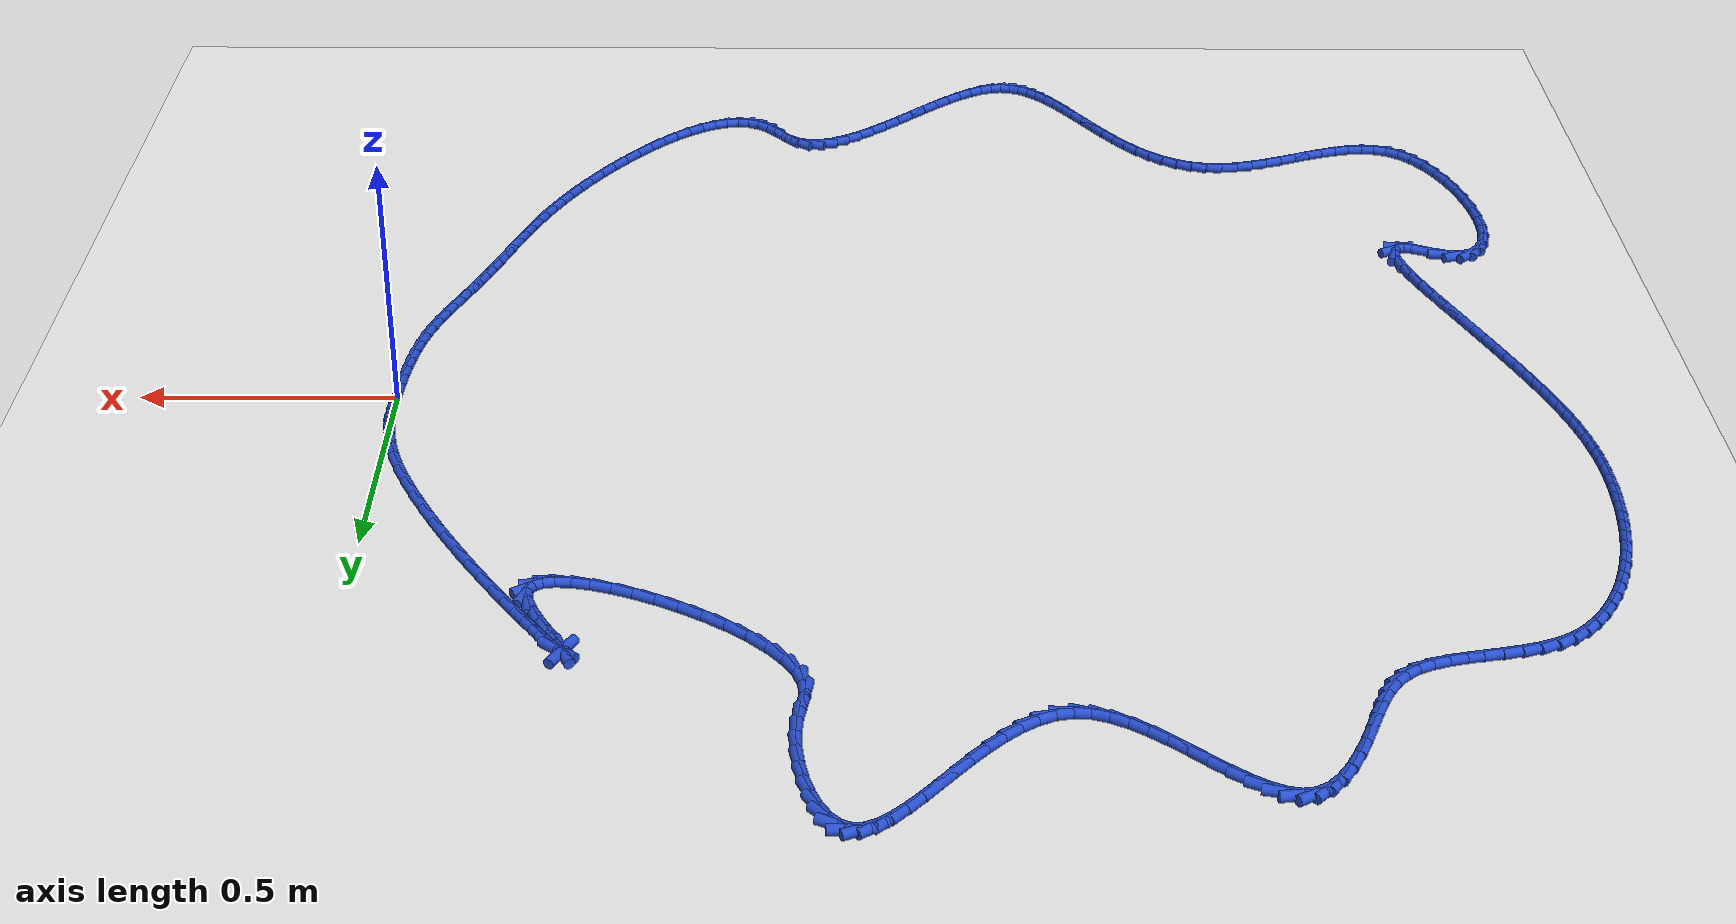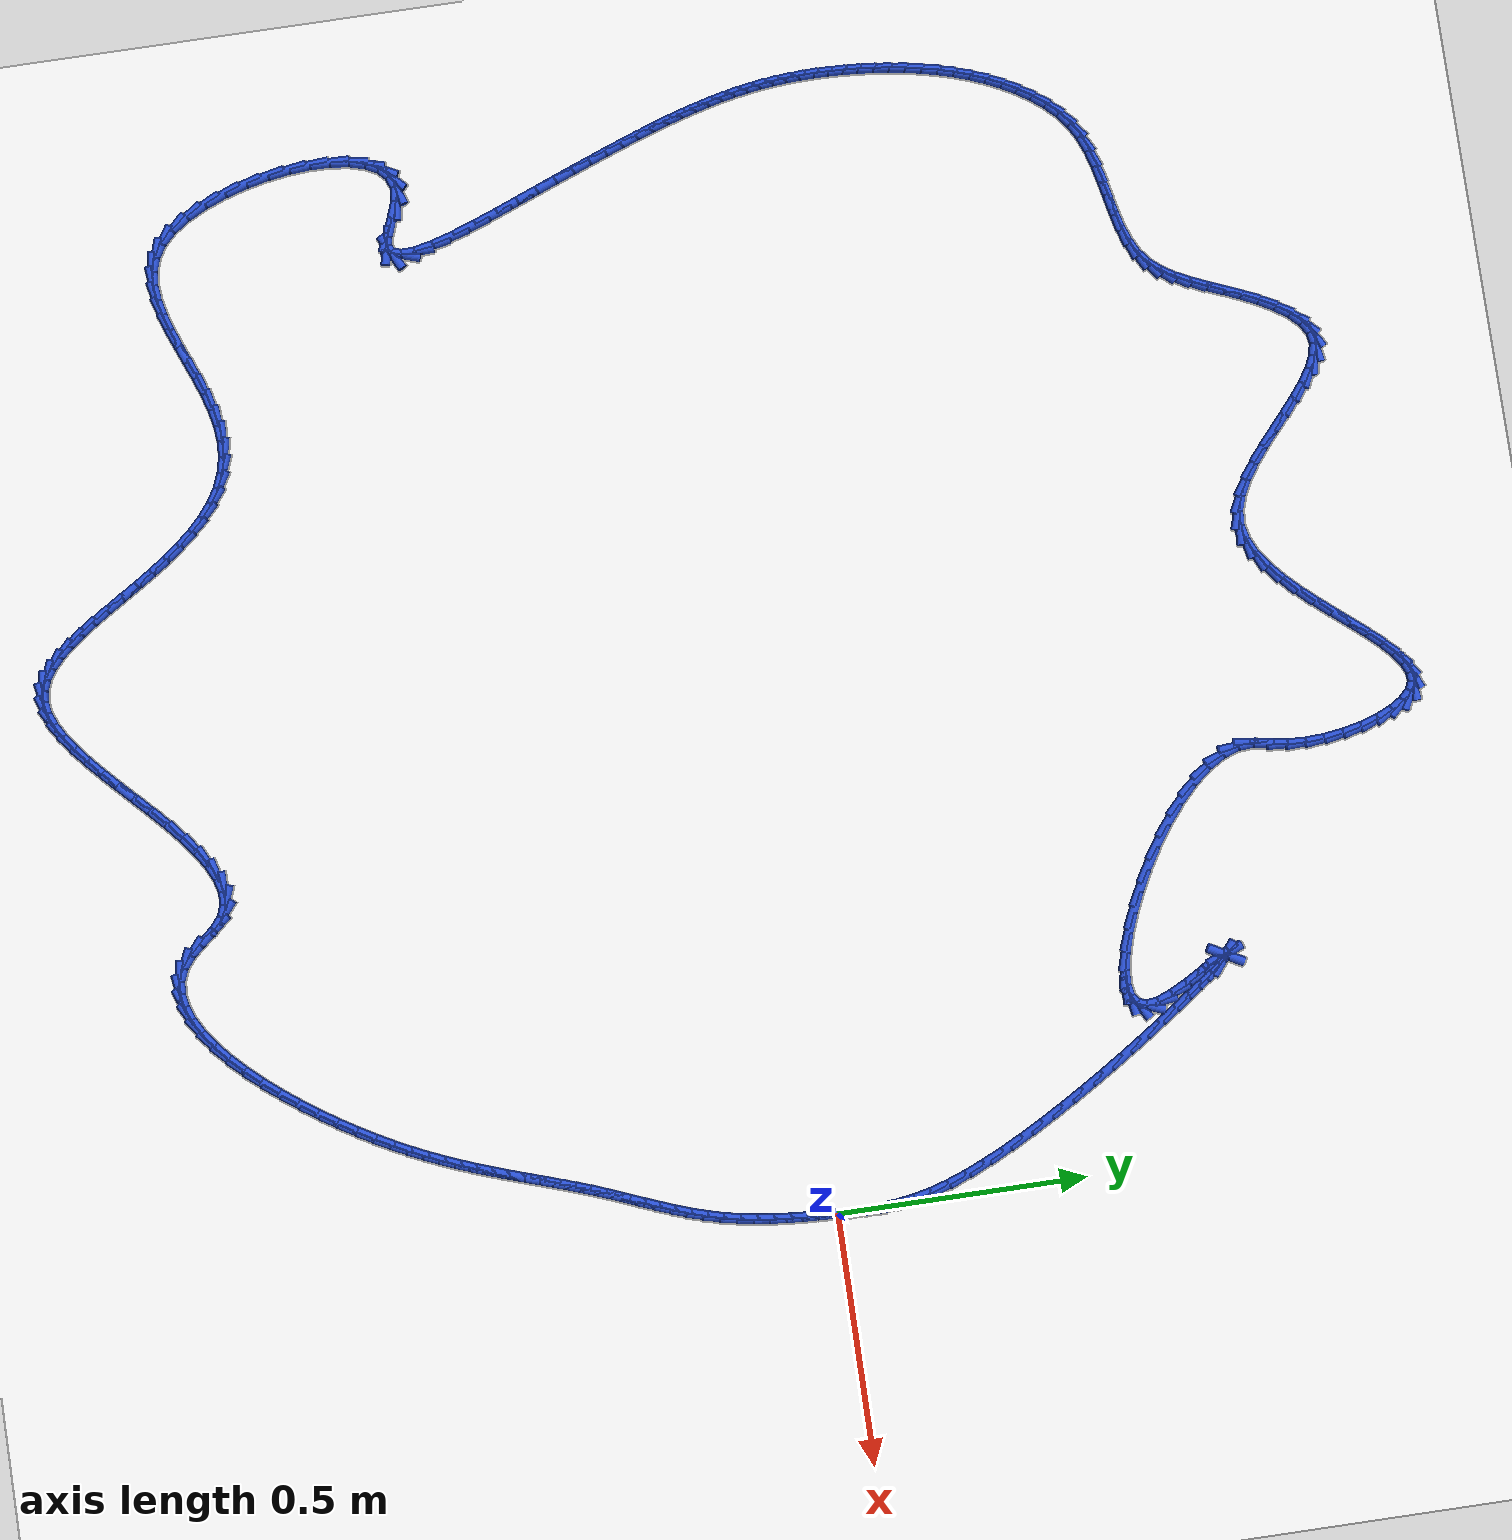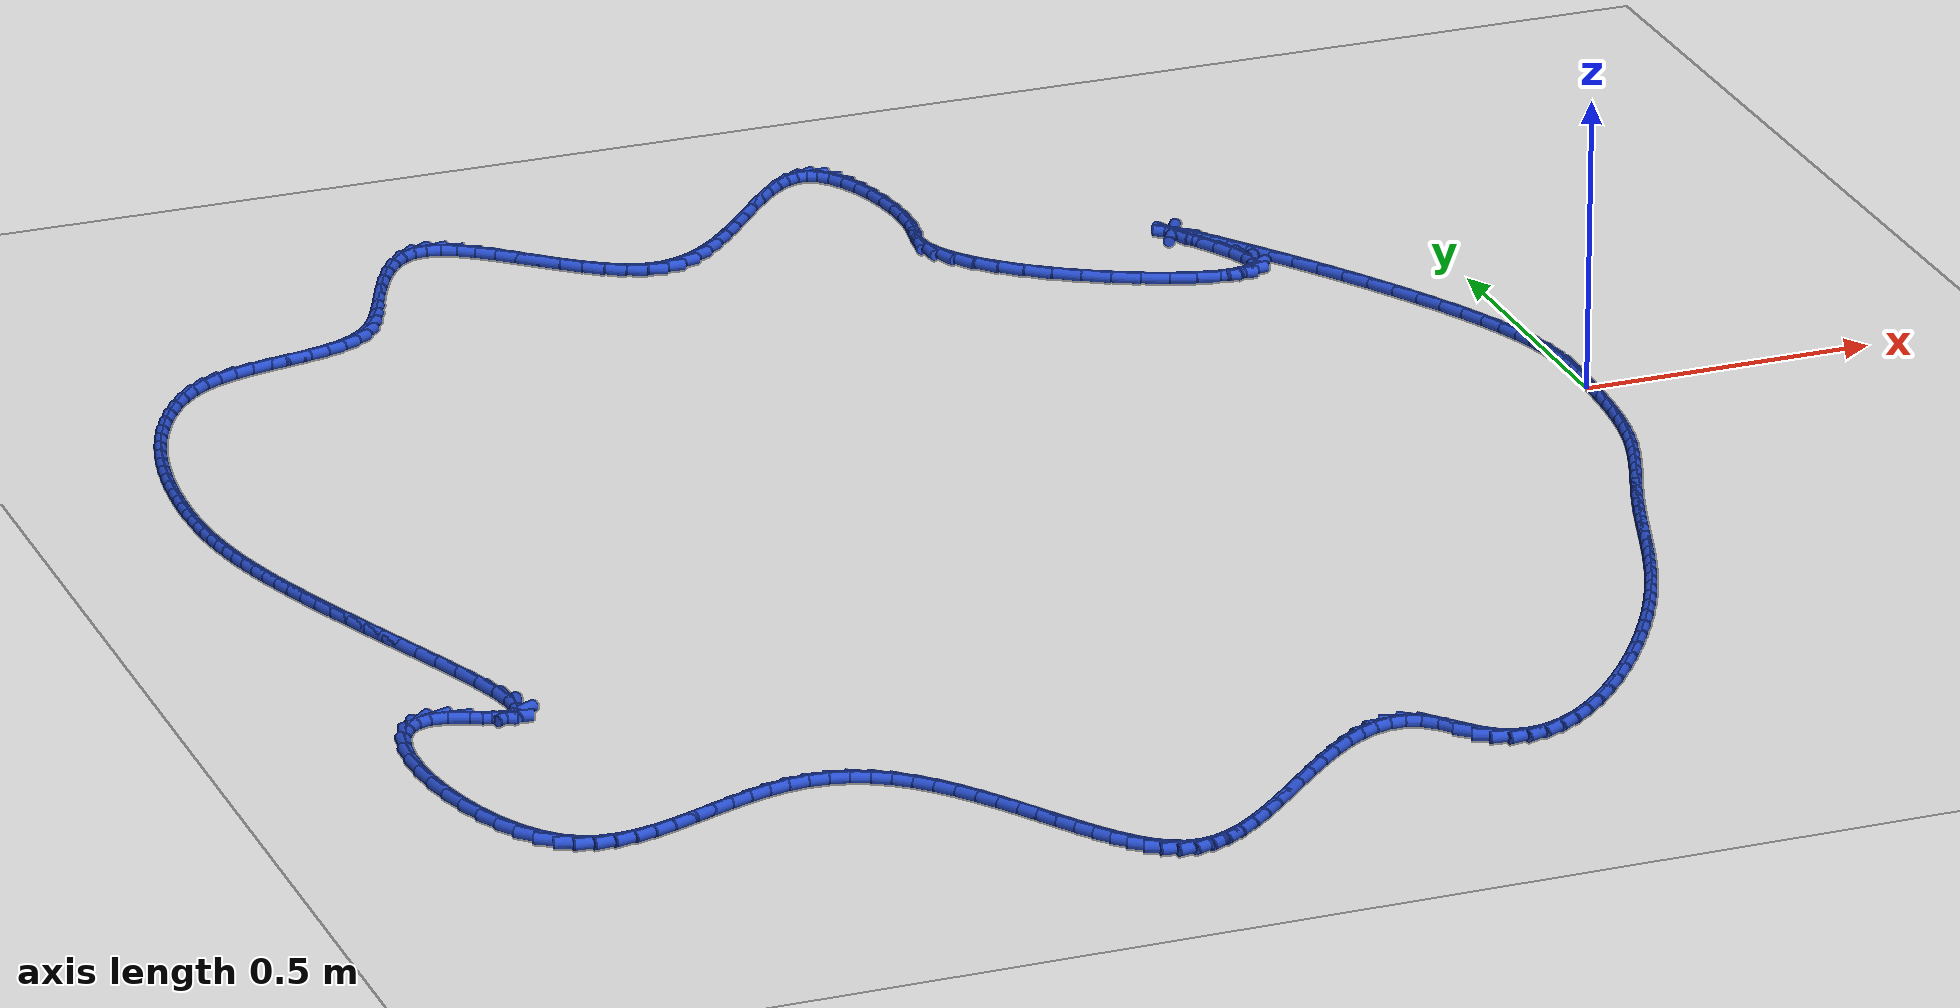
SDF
<sdf version="1.6">
 <world name="default">
  <light name="sun" type="directional">
   <pose>0 0 10 0 -0 0</pose>
   <diffuse>0.8 0.8 0.8 1</diffuse>
   <specular>0.2 0.2 0.2 1</specular>
   <attenuation>
    <range>1000</range>
    <constant>0.9</constant>
    <linear>0.01</linear>
    <quadratic>0.001</quadratic>
   </attenuation>
   <direction>-0.5 0.1 -0.9</direction>
  </light>
  <model name="ground_plane">
   <static>1</static>
   <link name="link">
    <collision name="collision">
     <geometry><plane><normal>0 0 1</normal><size>100 100</size></plane></geometry>
     <surface><friction><ode><mu>100</mu><mu2>50</mu2></ode></friction></surface>
    </collision>
    <visual name="visual">
     <cast_shadows>0</cast_shadows>
     <geometry><plane><normal>0 0 1</normal><size>100 100</size></plane></geometry>
     <material>
      <script><uri>file://media/materials/scripts/gazebo.material</uri><name>Gazebo/WhiteGlow</name></script>
     </material>
    </visual>
   </link>
  </model>
  <gravity>0 0 -9.8</gravity>
  <magnetic_field>6e-06 2.3e-05 -4.2e-05</magnetic_field>
  <atmosphere type="adiabatic"/>
  <physics name="default_physics" default="0" type="ode">
   <max_step_size>0.001</max_step_size>
   <real_time_factor>1</real_time_factor>
   <real_time_update_rate>1000</real_time_update_rate>
  </physics>
  <scene><ambient>0.4 0.4 0.4 1</ambient><background>0.7 0.7 0.7 1</background><shadows>1</shadows></scene>
  <spherical_coordinates>
   <surface_model>EARTH_WGS84</surface_model>
   <latitude_deg>0</latitude_deg>
   <longitude_deg>0</longitude_deg>
   <elevation>0</elevation>
   <heading_deg>0</heading_deg>
  </spherical_coordinates>
  <model name="line">
   <link name="link_0">
    <pose>-2.168404344971009e-18 5.551115123125783e-17 0.01 0 1.57 1.5390261016661055</pose>
    <collision name="collision">
     <geometry><cylinder><radius>0.01</radius><length>0.08</length></cylinder></geometry>
    </collision>
    <visual name="visual">
     <material>
      <script><name>Gazebo/Blue</name><uri>file://media/materials/scripts/gazebo.material</uri></script>
     </material>
     <geometry><cylinder><radius>0.01</radius><length>0.08</length></cylinder></geometry>
    </visual>
   </link>
   <link name="link_1">
    <pose>0.0009696372270421467 0.030510044156654634 0.01 0 1.57 1.5626794963856356</pose>
    <collision name="collision">
     <geometry><cylinder><radius>0.01</radius><length>0.08</length></cylinder></geometry>
    </collision>
    <visual name="visual">
     <material>
      <script><name>Gazebo/Blue</name><uri>file://media/materials/scripts/gazebo.material</uri></script>
     </material>
     <geometry><cylinder><radius>0.01</radius><length>0.08</length></cylinder></geometry>
    </visual>
   </link>
   <link name="link_2">
    <pose>0.0012147351030741545 0.06070563542335232 0.01 0 1.57 -1.5394462232085644</pose>
    <collision name="collision">
     <geometry><cylinder><radius>0.01</radius><length>0.08</length></cylinder></geometry>
    </collision>
    <visual name="visual">
     <material>
      <script><name>Gazebo/Blue</name><uri>file://media/materials/scripts/gazebo.material</uri></script>
     </material>
     <geometry><cylinder><radius>0.01</radius><length>0.08</length></cylinder></geometry>
    </visual>
   </link>
   <link name="link_3">
    <pose>0.0002617577878162975 0.09109357617121212 0.01 0 1.57 -1.486569121238892</pose>
    <collision name="collision">
     <geometry><cylinder><radius>0.01</radius><length>0.08</length></cylinder></geometry>
    </collision>
    <visual name="visual">
     <material>
      <script><name>Gazebo/Blue</name><uri>file://media/materials/scripts/gazebo.material</uri></script>
     </material>
     <geometry><cylinder><radius>0.01</radius><length>0.08</length></cylinder></geometry>
    </visual>
   </link>
   <link name="link_4">
    <pose>-0.00236283055901115 0.122180668771353 0.01 0 1.57 -1.4241549413371486</pose>
    <collision name="collision">
     <geometry><cylinder><radius>0.01</radius><length>0.08</length></cylinder></geometry>
    </collision>
    <visual name="visual">
     <material>
      <script><name>Gazebo/Blue</name><uri>file://media/materials/scripts/gazebo.material</uri></script>
     </material>
     <geometry><cylinder><radius>0.01</radius><length>0.08</length></cylinder></geometry>
    </visual>
   </link>
   <link name="link_5">
    <pose>-0.00713256577768791 0.15447371559489392 0.01 0 1.57 -1.3568521217161276</pose>
    <collision name="collision">
     <geometry><cylinder><radius>0.01</radius><length>0.08</length></cylinder></geometry>
    </collision>
    <visual name="visual">
     <material>
      <script><name>Gazebo/Blue</name><uri>file://media/materials/scripts/gazebo.material</uri></script>
     </material>
     <geometry><cylinder><radius>0.01</radius><length>0.08</length></cylinder></geometry>
    </visual>
   </link>
   <link name="link_6">
    <pose>-0.014520983708493715 0.188479519012954 0.01 0 1.57 -1.289168441655071</pose>
    <collision name="collision">
     <geometry><cylinder><radius>0.01</radius><length>0.08</length></cylinder></geometry>
    </collision>
    <visual name="visual">
     <material>
      <script><name>Gazebo/Blue</name><uri>file://media/materials/scripts/gazebo.material</uri></script>
     </material>
     <geometry><cylinder><radius>0.01</radius><length>0.08</length></cylinder></geometry>
    </visual>
   </link>
   <link name="link_7">
    <pose>-0.02500162019170828 0.22470488139665207 0.01 0 1.57 -1.2259756361821696</pose>
    <collision name="collision">
     <geometry><cylinder><radius>0.01</radius><length>0.08</length></cylinder></geometry>
    </collision>
    <visual name="visual">
     <material>
      <script><name>Gazebo/Blue</name><uri>file://media/materials/scripts/gazebo.material</uri></script>
     </material>
     <geometry><cylinder><radius>0.01</radius><length>0.08</length></cylinder></geometry>
    </visual>
   </link>
   <link name="link_8">
    <pose>-0.03895417391386646 0.2635515287089811 0.01 0 1.57 -1.1752619252486418</pose>
    <collision name="collision">
     <geometry><cylinder><radius>0.01</radius><length>0.08</length></cylinder></geometry>
    </collision>
    <visual name="visual">
     <material>
      <script><name>Gazebo/Blue</name><uri>file://media/materials/scripts/gazebo.material</uri></script>
     </material>
     <geometry><cylinder><radius>0.01</radius><length>0.08</length></cylinder></geometry>
    </visual>
   </link>
   <link name="link_9">
    <pose>-0.05615369847098064 0.3047441210411797 0.01 0 1.57 -1.1357443378032641</pose>
    <collision name="collision">
     <geometry><cylinder><radius>0.01</radius><length>0.08</length></cylinder></geometry>
    </collision>
    <visual name="visual">
     <material>
      <script><name>Gazebo/Blue</name><uri>file://media/materials/scripts/gazebo.material</uri></script>
     </material>
     <geometry><cylinder><radius>0.01</radius><length>0.08</length></cylinder></geometry>
    </visual>
   </link>
   <link name="link_10">
    <pose>-0.07613549073038313 0.3477388451253921 0.01 0 1.57 -1.1040338345905147</pose>
    <collision name="collision">
     <geometry><cylinder><radius>0.01</radius><length>0.08</length></cylinder></geometry>
    </collision>
    <visual name="visual">
     <material>
      <script><name>Gazebo/Blue</name><uri>file://media/materials/scripts/gazebo.material</uri></script>
     </material>
     <geometry><cylinder><radius>0.01</radius><length>0.08</length></cylinder></geometry>
    </visual>
   </link>
   <link name="link_11">
    <pose>-0.09843424539618331 0.3919912134070214 0.01 0 1.57 -1.0779209292897751</pose>
    <collision name="collision">
     <geometry><cylinder><radius>0.01</radius><length>0.08</length></cylinder></geometry>
    </collision>
    <visual name="visual">
     <material>
      <script><name>Gazebo/Blue</name><uri>file://media/materials/scripts/gazebo.material</uri></script>
     </material>
     <geometry><cylinder><radius>0.01</radius><length>0.08</length></cylinder></geometry>
    </visual>
   </link>
   <link name="link_12">
    <pose>-0.12258465717249051 0.43695673833147053 0.01 0 1.57 -1.055906318742567</pose>
    <collision name="collision">
     <geometry><cylinder><radius>0.01</radius><length>0.08</length></cylinder></geometry>
    </collision>
    <visual name="visual">
     <material>
      <script><name>Gazebo/Blue</name><uri>file://media/materials/scripts/gazebo.material</uri></script>
     </material>
     <geometry><cylinder><radius>0.01</radius><length>0.08</length></cylinder></geometry>
    </visual>
   </link>
   <link name="link_13">
    <pose>-0.14812142076341414 0.482090932344143 0.01 0 1.57 -1.0369278652685587</pose>
    <collision name="collision">
     <geometry><cylinder><radius>0.01</radius><length>0.08</length></cylinder></geometry>
    </collision>
    <visual name="visual">
     <material>
      <script><name>Gazebo/Blue</name><uri>file://media/materials/scripts/gazebo.material</uri></script>
     </material>
     <geometry><cylinder><radius>0.01</radius><length>0.08</length></cylinder></geometry>
    </visual>
   </link>
   <link name="link_14">
    <pose>-0.17457923087306362 0.5268493078904418 0.01 0 1.57 -1.0201963430898435</pose>
    <collision name="collision">
     <geometry><cylinder><radius>0.01</radius><length>0.08</length></cylinder></geometry>
    </collision>
    <visual name="visual">
     <material>
      <script><name>Gazebo/Blue</name><uri>file://media/materials/scripts/gazebo.material</uri></script>
     </material>
     <geometry><cylinder><radius>0.01</radius><length>0.08</length></cylinder></geometry>
    </visual>
   </link>
   <link name="link_15">
    <pose>-0.2014927822055482 0.5706873774157702 0.01 0 1.57 -1.0050894761050686</pose>
    <collision name="collision">
     <geometry><cylinder><radius>0.01</radius><length>0.08</length></cylinder></geometry>
    </collision>
    <visual name="visual">
     <material>
      <script><name>Gazebo/Blue</name><uri>file://media/materials/scripts/gazebo.material</uri></script>
     </material>
     <geometry><cylinder><radius>0.01</radius><length>0.08</length></cylinder></geometry>
    </visual>
   </link>
   <link name="link_16">
    <pose>-0.22839676946497742 0.6130606533655312 0.01 0 1.57 -0.9910754203302397</pose>
    <collision name="collision">
     <geometry><cylinder><radius>0.01</radius><length>0.08</length></cylinder></geometry>
    </collision>
    <visual name="visual">
     <material>
      <script><name>Gazebo/Blue</name><uri>file://media/materials/scripts/gazebo.material</uri></script>
     </material>
     <geometry><cylinder><radius>0.01</radius><length>0.08</length></cylinder></geometry>
    </visual>
   </link>
   <link name="link_17">
    <pose>-0.2548258873554605 0.6534246481851281 0.01 0 1.57 -0.9776457558575486</pose>
    <collision name="collision">
     <geometry><cylinder><radius>0.01</radius><length>0.08</length></cylinder></geometry>
    </collision>
    <visual name="visual">
     <material>
      <script><name>Gazebo/Blue</name><uri>file://media/materials/scripts/gazebo.material</uri></script>
     </material>
     <geometry><cylinder><radius>0.01</radius><length>0.08</length></cylinder></geometry>
    </visual>
   </link>
   <link name="link_18">
    <pose>-0.28031483058110684 0.6912348743199638 0.01 0 1.57 -0.9642377615726986</pose>
    <collision name="collision">
     <geometry><cylinder><radius>0.01</radius><length>0.08</length></cylinder></geometry>
    </collision>
    <visual name="visual">
     <material>
      <script><name>Gazebo/Blue</name><uri>file://media/materials/scripts/gazebo.material</uri></script>
     </material>
     <geometry><cylinder><radius>0.01</radius><length>0.08</length></cylinder></geometry>
    </visual>
   </link>
   <link name="link_19">
    <pose>-0.304398293846026 0.7259468442154421 0.01 0 1.57 -0.9501127625240884</pose>
    <collision name="collision">
     <geometry><cylinder><radius>0.01</radius><length>0.08</length></cylinder></geometry>
    </collision>
    <visual name="visual">
     <material>
      <script><name>Gazebo/Blue</name><uri>file://media/materials/scripts/gazebo.material</uri></script>
     </material>
     <geometry><cylinder><radius>0.01</radius><length>0.08</length></cylinder></geometry>
    </visual>
   </link>
   <link name="link_20">
    <pose>-0.326610971854327 0.7570160703169653 0.01 0 1.57 -0.9341128309318267</pose>
    <collision name="collision">
     <geometry><cylinder><radius>0.01</radius><length>0.08</length></cylinder></geometry>
    </collision>
    <visual name="visual">
     <material>
      <script><name>Gazebo/Blue</name><uri>file://media/materials/scripts/gazebo.material</uri></script>
     </material>
     <geometry><cylinder><radius>0.01</radius><length>0.08</length></cylinder></geometry>
    </visual>
   </link>
   <link name="link_21">
    <pose>-0.3464875593101196 0.7838980650699371 0.01 0 1.57 -0.914065761521262</pose>
    <collision name="collision">
     <geometry><cylinder><radius>0.01</radius><length>0.08</length></cylinder></geometry>
    </collision>
    <visual name="visual">
     <material>
      <script><name>Gazebo/Blue</name><uri>file://media/materials/scripts/gazebo.material</uri></script>
     </material>
     <geometry><cylinder><radius>0.01</radius><length>0.08</length></cylinder></geometry>
    </visual>
   </link>
   <link name="link_22">
    <pose>-0.3635627509175131 0.8060483409197607 0.01 0 1.57 -0.8849804289008176</pose>
    <collision name="collision">
     <geometry><cylinder><radius>0.01</radius><length>0.08</length></cylinder></geometry>
    </collision>
    <visual name="visual">
     <material>
      <script><name>Gazebo/Blue</name><uri>file://media/materials/scripts/gazebo.material</uri></script>
     </material>
     <geometry><cylinder><radius>0.01</radius><length>0.08</length></cylinder></geometry>
    </visual>
   </link>
   <link name="link_23">
    <pose>-0.37737124138061656 0.8229224103118391 0.01 0 1.57 -0.8315980081431773</pose>
    <collision name="collision">
     <geometry><cylinder><radius>0.01</radius><length>0.08</length></cylinder></geometry>
    </collision>
    <visual name="visual">
     <material>
      <script><name>Gazebo/Blue</name><uri>file://media/materials/scripts/gazebo.material</uri></script>
     </material>
     <geometry><cylinder><radius>0.01</radius><length>0.08</length></cylinder></geometry>
    </visual>
   </link>
   <link name="link_24">
    <pose>-0.38744772540353967 0.8339757856915754 0.01 0 1.57 -0.6731683115903806</pose>
    <collision name="collision">
     <geometry><cylinder><radius>0.01</radius><length>0.08</length></cylinder></geometry>
    </collision>
    <visual name="visual">
     <material>
      <script><name>Gazebo/Blue</name><uri>file://media/materials/scripts/gazebo.material</uri></script>
     </material>
     <geometry><cylinder><radius>0.01</radius><length>0.08</length></cylinder></geometry>
    </visual>
   </link>
   <link name="link_25">
    <pose>-0.39332689769039164 0.838663979504373 0.01 0 1.57 1.0697714906747218</pose>
    <collision name="collision">
     <geometry><cylinder><radius>0.01</radius><length>0.08</length></cylinder></geometry>
    </collision>
    <visual name="visual">
     <material>
      <script><name>Gazebo/Blue</name><uri>file://media/materials/scripts/gazebo.material</uri></script>
     </material>
     <geometry><cylinder><radius>0.01</radius><length>0.08</length></cylinder></geometry>
    </visual>
   </link>
   <link name="link_26">
    <pose>-0.39454345294528204 0.8364425041956347 0.01 0 1.57 -1.186632170181604</pose>
    <collision name="collision">
     <geometry><cylinder><radius>0.01</radius><length>0.08</length></cylinder></geometry>
    </collision>
    <visual name="visual">
     <material>
      <script><name>Gazebo/Blue</name><uri>file://media/materials/scripts/gazebo.material</uri></script>
     </material>
     <geometry><cylinder><radius>0.01</radius><length>0.08</length></cylinder></geometry>
    </visual>
   </link>
   <link name="link_27">
    <pose>-0.39063208587232 0.8267668722107641 0.01 0 1.57 -1.0773956384388206</pose>
    <collision name="collision">
     <geometry><cylinder><radius>0.01</radius><length>0.08</length></cylinder></geometry>
    </collision>
    <visual name="visual">
     <material>
      <script><name>Gazebo/Blue</name><uri>file://media/materials/scripts/gazebo.material</uri></script>
     </material>
     <geometry><cylinder><radius>0.01</radius><length>0.08</length></cylinder></geometry>
    </visual>
   </link>
   <link name="link_28">
    <pose>-0.38112749117561506 0.809092595995164 0.01 0 1.57 -1.042465320660573</pose>
    <collision name="collision">
     <geometry><cylinder><radius>0.01</radius><length>0.08</length></cylinder></geometry>
    </collision>
    <visual name="visual">
     <material>
      <script><name>Gazebo/Blue</name><uri>file://media/materials/scripts/gazebo.material</uri></script>
     </material>
     <geometry><cylinder><radius>0.01</radius><length>0.08</length></cylinder></geometry>
    </visual>
   </link>
   <link name="link_29">
    <pose>-0.3661862423763073 0.7834941184664659 0.01 0 1.57 -1.053773762595295</pose>
    <collision name="collision">
     <geometry><cylinder><radius>0.01</radius><length>0.08</length></cylinder></geometry>
    </collision>
    <visual name="visual">
     <material>
      <script><name>Gazebo/Blue</name><uri>file://media/materials/scripts/gazebo.material</uri></script>
     </material>
     <geometry><cylinder><radius>0.01</radius><length>0.08</length></cylinder></geometry>
    </visual>
   </link>
   <link name="link_30">
    <pose>-0.34873435090351856 0.7528021904679787 0.01 0 1.57 -1.1028815049736527</pose>
    <collision name="collision">
     <geometry><cylinder><radius>0.01</radius><length>0.08</length></cylinder></geometry>
    </collision>
    <visual name="visual">
     <material>
      <script><name>Gazebo/Blue</name><uri>file://media/materials/scripts/gazebo.material</uri></script>
     </material>
     <geometry><cylinder><radius>0.01</radius><length>0.08</length></cylinder></geometry>
    </visual>
   </link>
   <link name="link_31">
    <pose>-0.3324684773406483 0.7206145583281722 0.01 0 1.57 -1.2090834098077756</pose>
    <collision name="collision">
     <geometry><cylinder><radius>0.01</radius><length>0.08</length></cylinder></geometry>
    </collision>
    <visual name="visual">
     <material>
      <script><name>Gazebo/Blue</name><uri>file://media/materials/scripts/gazebo.material</uri></script>
     </material>
     <geometry><cylinder><radius>0.01</radius><length>0.08</length></cylinder></geometry>
    </visual>
   </link>
   <link name="link_32">
    <pose>-0.3210853139922979 0.6905289999463264 0.01 0 1.57 -1.4529396408153854</pose>
    <collision name="collision">
     <geometry><cylinder><radius>0.01</radius><length>0.08</length></cylinder></geometry>
    </collision>
    <visual name="visual">
     <material>
      <script><name>Gazebo/Blue</name><uri>file://media/materials/scripts/gazebo.material</uri></script>
     </material>
     <geometry><cylinder><radius>0.01</radius><length>0.08</length></cylinder></geometry>
    </visual>
   </link>
   <link name="link_33">
    <pose>-0.31818871235353396 0.6660655787837115 0.01 0 1.57 1.1904567449538879</pose>
    <collision name="collision">
     <geometry><cylinder><radius>0.01</radius><length>0.08</length></cylinder></geometry>
    </collision>
    <visual name="visual">
     <material>
      <script><name>Gazebo/Blue</name><uri>file://media/materials/scripts/gazebo.material</uri></script>
     </material>
     <geometry><cylinder><radius>0.01</radius><length>0.08</length></cylinder></geometry>
    </visual>
   </link>
   <link name="link_34">
    <pose>-0.32508360745226117 0.6488199997983508 0.01 0 1.57 0.589653028405353</pose>
    <collision name="collision">
     <geometry><cylinder><radius>0.01</radius><length>0.08</length></cylinder></geometry>
    </collision>
    <visual name="visual">
     <material>
      <script><name>Gazebo/Blue</name><uri>file://media/materials/scripts/gazebo.material</uri></script>
     </material>
     <geometry><cylinder><radius>0.01</radius><length>0.08</length></cylinder></geometry>
    </visual>
   </link>
   <link name="link_35">
    <pose>-0.340681292859557 0.6383843178126629 0.01 0 1.57 0.1768060039253963</pose>
    <collision name="collision">
     <geometry><cylinder><radius>0.01</radius><length>0.08</length></cylinder></geometry>
    </collision>
    <visual name="visual">
     <material>
      <script><name>Gazebo/Blue</name><uri>file://media/materials/scripts/gazebo.material</uri></script>
     </material>
     <geometry><cylinder><radius>0.01</radius><length>0.08</length></cylinder></geometry>
    </visual>
   </link>
   <link name="link_36">
    <pose>-0.3637812666558643 0.6342570067790777 0.01 0 1.57 -0.05706157022969296</pose>
    <collision name="collision">
     <geometry><cylinder><radius>0.01</radius><length>0.08</length></cylinder></geometry>
    </collision>
    <visual name="visual">
     <material>
      <script><name>Gazebo/Blue</name><uri>file://media/materials/scripts/gazebo.material</uri></script>
     </material>
     <geometry><cylinder><radius>0.01</radius><length>0.08</length></cylinder></geometry>
    </visual>
   </link>
   <link name="link_37">
    <pose>-0.3931830269216252 0.6359365406500256 0.01 0 1.57 -0.19974217751282627</pose>
    <collision name="collision">
     <geometry><cylinder><radius>0.01</radius><length>0.08</length></cylinder></geometry>
    </collision>
    <visual name="visual">
     <material>
      <script><name>Gazebo/Blue</name><uri>file://media/materials/scripts/gazebo.material</uri></script>
     </material>
     <geometry><cylinder><radius>0.01</radius><length>0.08</length></cylinder></geometry>
    </visual>
   </link>
   <link name="link_38">
    <pose>-0.42768607173728235 0.6429213933779364 0.01 0 1.57 -0.2978347389365399</pose>
    <collision name="collision">
     <geometry><cylinder><radius>0.01</radius><length>0.08</length></cylinder></geometry>
    </collision>
    <visual name="visual">
     <material>
      <script><name>Gazebo/Blue</name><uri>file://media/materials/scripts/gazebo.material</uri></script>
     </material>
     <geometry><cylinder><radius>0.01</radius><length>0.08</length></cylinder></geometry>
    </visual>
   </link>
   <link name="link_39">
    <pose>-0.4660898991832781 0.6547100389152407 0.01 0 1.57 -0.3731289873238947</pose>
    <collision name="collision">
     <geometry><cylinder><radius>0.01</radius><length>0.08</length></cylinder></geometry>
    </collision>
    <visual name="visual">
     <material>
      <script><name>Gazebo/Blue</name><uri>file://media/materials/scripts/gazebo.material</uri></script>
     </material>
     <geometry><cylinder><radius>0.01</radius><length>0.08</length></cylinder></geometry>
    </visual>
   </link>
   <link name="link_40">
    <pose>-0.5071940073400548 0.6708009512143681 0.01 0 1.57 -0.43681678667540025</pose>
    <collision name="collision">
     <geometry><cylinder><radius>0.01</radius><length>0.08</length></cylinder></geometry>
    </collision>
    <visual name="visual">
     <material>
      <script><name>Gazebo/Blue</name><uri>file://media/materials/scripts/gazebo.material</uri></script>
     </material>
     <geometry><cylinder><radius>0.01</radius><length>0.08</length></cylinder></geometry>
    </visual>
   </link>
   <link name="link_41">
    <pose>-0.5497978942880554 0.690692604227749 0.01 0 1.57 -0.4955511020099694</pose>
    <collision name="collision">
     <geometry><cylinder><radius>0.01</radius><length>0.08</length></cylinder></geometry>
    </collision>
    <visual name="visual">
     <material>
      <script><name>Gazebo/Blue</name><uri>file://media/materials/scripts/gazebo.material</uri></script>
     </material>
     <geometry><cylinder><radius>0.01</radius><length>0.08</length></cylinder></geometry>
    </visual>
   </link>
   <link name="link_42">
    <pose>-0.5927010581077218 0.7138834719078133 0.01 0 1.57 -0.5540898361481409</pose>
    <collision name="collision">
     <geometry><cylinder><radius>0.01</radius><length>0.08</length></cylinder></geometry>
    </collision>
    <visual name="visual">
     <material>
      <script><name>Gazebo/Blue</name><uri>file://media/materials/scripts/gazebo.material</uri></script>
     </material>
     <geometry><cylinder><radius>0.01</radius><length>0.08</length></cylinder></geometry>
    </visual>
   </link>
   <link name="link_43">
    <pose>-0.6347029968794969 0.7398720282069915 0.01 0 1.57 -0.6166651489633308</pose>
    <collision name="collision">
     <geometry><cylinder><radius>0.01</radius><length>0.08</length></cylinder></geometry>
    </collision>
    <visual name="visual">
     <material>
      <script><name>Gazebo/Blue</name><uri>file://media/materials/scripts/gazebo.material</uri></script>
     </material>
     <geometry><cylinder><radius>0.01</radius><length>0.08</length></cylinder></geometry>
    </visual>
   </link>
   <link name="link_44">
    <pose>-0.674603208683823 0.7681567470777132 0.01 0 1.57 -0.6879440933231683</pose>
    <collision name="collision">
     <geometry><cylinder><radius>0.01</radius><length>0.08</length></cylinder></geometry>
    </collision>
    <visual name="visual">
     <material>
      <script><name>Gazebo/Blue</name><uri>file://media/materials/scripts/gazebo.material</uri></script>
     </material>
     <geometry><cylinder><radius>0.01</radius><length>0.08</length></cylinder></geometry>
    </visual>
   </link>
   <link name="link_45">
    <pose>-0.7112011916011425 0.7982361024724087 0.01 0 1.57 -0.7740104056761873</pose>
    <collision name="collision">
     <geometry><cylinder><radius>0.01</radius><length>0.08</length></cylinder></geometry>
    </collision>
    <visual name="visual">
     <material>
      <script><name>Gazebo/Blue</name><uri>file://media/materials/scripts/gazebo.material</uri></script>
     </material>
     <geometry><cylinder><radius>0.01</radius><length>0.08</length></cylinder></geometry>
    </visual>
   </link>
   <link name="link_46">
    <pose>-0.7432964437118977 0.8296085683435082 0.01 0 1.57 -0.8836534661181015</pose>
    <collision name="collision">
     <geometry><cylinder><radius>0.01</radius><length>0.08</length></cylinder></geometry>
    </collision>
    <visual name="visual">
     <material>
      <script><name>Gazebo/Blue</name><uri>file://media/materials/scripts/gazebo.material</uri></script>
     </material>
     <geometry><cylinder><radius>0.01</radius><length>0.08</length></cylinder></geometry>
    </visual>
   </link>
   <link name="link_47">
    <pose>-0.7696884630965315 0.8617726186434418 0.01 0 1.57 -1.0300184895804152</pose>
    <collision name="collision">
     <geometry><cylinder><radius>0.01</radius><length>0.08</length></cylinder></geometry>
    </collision>
    <visual name="visual">
     <material>
      <script><name>Gazebo/Blue</name><uri>file://media/materials/scripts/gazebo.material</uri></script>
     </material>
     <geometry><cylinder><radius>0.01</radius><length>0.08</length></cylinder></geometry>
    </visual>
   </link>
   <link name="link_48">
    <pose>-0.789176747835486 0.8942267273246394 0.01 0 1.57 -1.2313853323790753</pose>
    <collision name="collision">
     <geometry><cylinder><radius>0.01</radius><length>0.08</length></cylinder></geometry>
    </collision>
    <visual name="visual">
     <material>
      <script><name>Gazebo/Blue</name><uri>file://media/materials/scripts/gazebo.material</uri></script>
     </material>
     <geometry><cylinder><radius>0.01</radius><length>0.08</length></cylinder></geometry>
    </visual>
   </link>
   <link name="link_49">
    <pose>-0.8005607960092038 0.9264693683395312 0.01 0 1.57 -1.5021331663104622</pose>
    <collision name="collision">
     <geometry><cylinder><radius>0.01</radius><length>0.08</length></cylinder></geometry>
    </collision>
    <visual name="visual">
     <material>
      <script><name>Gazebo/Blue</name><uri>file://media/materials/scripts/gazebo.material</uri></script>
     </material>
     <geometry><cylinder><radius>0.01</radius><length>0.08</length></cylinder></geometry>
    </visual>
   </link>
   <link name="link_50">
    <pose>-0.8027313823046557 0.9580317671190492 0.01 0 1.57 1.4180306053113454</pose>
    <collision name="collision">
     <geometry><cylinder><radius>0.01</radius><length>0.08</length></cylinder></geometry>
    </collision>
    <visual name="visual">
     <material>
      <script><name>Gazebo/Blue</name><uri>file://media/materials/scripts/gazebo.material</uri></script>
     </material>
     <geometry><cylinder><radius>0.01</radius><length>0.08</length></cylinder></geometry>
    </visual>
   </link>
   <link name="link_51">
    <pose>-0.797867138492566 0.9896248838004381 0.01 0 1.57 1.4061586394690828</pose>
    <collision name="collision">
     <geometry><cylinder><radius>0.01</radius><length>0.08</length></cylinder></geometry>
    </collision>
    <visual name="visual">
     <material>
      <script><name>Gazebo/Blue</name><uri>file://media/materials/scripts/gazebo.material</uri></script>
     </material>
     <geometry><cylinder><radius>0.01</radius><length>0.08</length></cylinder></geometry>
    </visual>
   </link>
   <link name="link_52">
    <pose>-0.792251040381194 1.0234279805328215 0.01 0 1.57 1.5149853746097552</pose>
    <collision name="collision">
     <geometry><cylinder><radius>0.01</radius><length>0.08</length></cylinder></geometry>
    </collision>
    <visual name="visual">
     <material>
      <script><name>Gazebo/Blue</name><uri>file://media/materials/scripts/gazebo.material</uri></script>
     </material>
     <geometry><cylinder><radius>0.01</radius><length>0.08</length></cylinder></geometry>
    </visual>
   </link>
   <link name="link_53">
    <pose>-0.7901823507023541 1.060455503934877 0.01 0 1.57 -1.5293515457072289</pose>
    <collision name="collision">
     <geometry><cylinder><radius>0.01</radius><length>0.08</length></cylinder></geometry>
    </collision>
    <visual name="visual">
     <material>
      <script><name>Gazebo/Blue</name><uri>file://media/materials/scripts/gazebo.material</uri></script>
     </material>
     <geometry><cylinder><radius>0.01</radius><length>0.08</length></cylinder></geometry>
    </visual>
   </link>
   <link name="link_54">
    <pose>-0.7917968211206052 1.0993879314758261 0.01 0 1.57 -1.4446012060952833</pose>
    <collision name="collision">
     <geometry><cylinder><radius>0.01</radius><length>0.08</length></cylinder></geometry>
    </collision>
    <visual name="visual">
     <material>
      <script><name>Gazebo/Blue</name><uri>file://media/materials/scripts/gazebo.material</uri></script>
     </material>
     <geometry><cylinder><radius>0.01</radius><length>0.08</length></cylinder></geometry>
    </visual>
   </link>
   <link name="link_55">
    <pose>-0.7967782773159612 1.1386524012464836 0.01 0 1.57 -1.36261298165159</pose>
    <collision name="collision">
     <geometry><cylinder><radius>0.01</radius><length>0.08</length></cylinder></geometry>
    </collision>
    <visual name="visual">
     <material>
      <script><name>Gazebo/Blue</name><uri>file://media/materials/scripts/gazebo.material</uri></script>
     </material>
     <geometry><cylinder><radius>0.01</radius><length>0.08</length></cylinder></geometry>
    </visual>
   </link>
   <link name="link_56">
    <pose>-0.8048105449684372 1.1766760513376644 0.01 0 1.57 -1.2740348467215763</pose>
    <collision name="collision">
     <geometry><cylinder><radius>0.01</radius><length>0.08</length></cylinder></geometry>
    </collision>
    <visual name="visual">
     <material>
      <script><name>Gazebo/Blue</name><uri>file://media/materials/scripts/gazebo.material</uri></script>
     </material>
     <geometry><cylinder><radius>0.01</radius><length>0.08</length></cylinder></geometry>
    </visual>
   </link>
   <link name="link_57">
    <pose>-0.8155774497580461 1.2118860198401835 0.01 0 1.57 -1.1665809531986697</pose>
    <collision name="collision">
     <geometry><cylinder><radius>0.01</radius><length>0.08</length></cylinder></geometry>
    </collision>
    <visual name="visual">
     <material>
      <script><name>Gazebo/Blue</name><uri>file://media/materials/scripts/gazebo.material</uri></script>
     </material>
     <geometry><cylinder><radius>0.01</radius><length>0.08</length></cylinder></geometry>
    </visual>
   </link>
   <link name="link_58">
    <pose>-0.8287628173648032 1.2427094448448561 0.01 0 1.57 -1.0195288065338302</pose>
    <collision name="collision">
     <geometry><cylinder><radius>0.01</radius><length>0.08</length></cylinder></geometry>
    </collision>
    <visual name="visual">
     <material>
      <script><name>Gazebo/Blue</name><uri>file://media/materials/scripts/gazebo.material</uri></script>
     </material>
     <geometry><cylinder><radius>0.01</radius><length>0.08</length></cylinder></geometry>
    </visual>
   </link>
   <link name="link_59">
    <pose>-0.844050473468722 1.267573464442497 0.01 0 1.57 -0.7928962958582678</pose>
    <collision name="collision">
     <geometry><cylinder><radius>0.01</radius><length>0.08</length></cylinder></geometry>
    </collision>
    <visual name="visual">
     <material>
      <script><name>Gazebo/Blue</name><uri>file://media/materials/scripts/gazebo.material</uri></script>
     </material>
     <geometry><cylinder><radius>0.01</radius><length>0.08</length></cylinder></geometry>
    </visual>
   </link>
   <link name="link_60">
    <pose>-0.8611242437498168 1.2849052167239212 0.01 0 1.57 -0.4187631222393703</pose>
    <collision name="collision">
     <geometry><cylinder><radius>0.01</radius><length>0.08</length></cylinder></geometry>
    </collision>
    <visual name="visual">
     <material>
      <script><name>Gazebo/Blue</name><uri>file://media/materials/scripts/gazebo.material</uri></script>
     </material>
     <geometry><cylinder><radius>0.01</radius><length>0.08</length></cylinder></geometry>
    </visual>
   </link>
   <link name="link_61">
    <pose>-0.8796703761342545 1.2931599114465782 0.01 0 1.57 0.060290091999281405</pose>
    <collision name="collision">
     <geometry><cylinder><radius>0.01</radius><length>0.08</length></cylinder></geometry>
    </collision>
    <visual name="visual">
     <material>
      <script><name>Gazebo/Blue</name><uri>file://media/materials/scripts/gazebo.material</uri></script>
     </material>
     <geometry><cylinder><radius>0.01</radius><length>0.08</length></cylinder></geometry>
    </visual>
   </link>
   <link name="link_62">
    <pose>-0.8994762142151558 1.291964366735504 0.01 0 1.57 0.42301511139550524</pose>
    <collision name="collision">
     <geometry><cylinder><radius>0.01</radius><length>0.08</length></cylinder></geometry>
    </collision>
    <visual name="visual">
     <material>
      <script><name>Gazebo/Blue</name><uri>file://media/materials/scripts/gazebo.material</uri></script>
     </material>
     <geometry><cylinder><radius>0.01</radius><length>0.08</length></cylinder></geometry>
    </visual>
   </link>
   <link name="link_63">
    <pose>-0.9204645849325938 1.282515531540735 0.01 0 1.57 0.6382057872704682</pose>
    <collision name="collision">
     <geometry><cylinder><radius>0.01</radius><length>0.08</length></cylinder></geometry>
    </collision>
    <visual name="visual">
     <material>
      <script><name>Gazebo/Blue</name><uri>file://media/materials/scripts/gazebo.material</uri></script>
     </material>
     <geometry><cylinder><radius>0.01</radius><length>0.08</length></cylinder></geometry>
    </visual>
   </link>
   <link name="link_64">
    <pose>-0.9425678003503201 1.2661202789129573 0.01 0 1.57 0.7607142104542608</pose>
    <collision name="collision">
     <geometry><cylinder><radius>0.01</radius><length>0.08</length></cylinder></geometry>
    </collision>
    <visual name="visual">
     <material>
      <script><name>Gazebo/Blue</name><uri>file://media/materials/scripts/gazebo.material</uri></script>
     </material>
     <geometry><cylinder><radius>0.01</radius><length>0.08</length></cylinder></geometry>
    </visual>
   </link>
   <link name="link_65">
    <pose>-0.9657181725320864 1.2440854819028568 0.01 0 1.57 0.8296810079567392</pose>
    <collision name="collision">
     <geometry><cylinder><radius>0.01</radius><length>0.08</length></cylinder></geometry>
    </collision>
    <visual name="visual">
     <material>
      <script><name>Gazebo/Blue</name><uri>file://media/materials/scripts/gazebo.material</uri></script>
     </material>
     <geometry><cylinder><radius>0.01</radius><length>0.08</length></cylinder></geometry>
    </visual>
   </link>
   <link name="link_66">
    <pose>-0.9898480135416446 1.2177180135611205 0.01 0 1.57 0.8651707159796929</pose>
    <collision name="collision">
     <geometry><cylinder><radius>0.01</radius><length>0.08</length></cylinder></geometry>
    </collision>
    <visual name="visual">
     <material>
      <script><name>Gazebo/Blue</name><uri>file://media/materials/scripts/gazebo.material</uri></script>
     </material>
     <geometry><cylinder><radius>0.01</radius><length>0.08</length></cylinder></geometry>
    </visual>
   </link>
   <link name="link_67">
    <pose>-1.0148896354427461 1.1883247469384344 0.01 0 1.57 0.8768384008983708</pose>
    <collision name="collision">
     <geometry><cylinder><radius>0.01</radius><length>0.08</length></cylinder></geometry>
    </collision>
    <visual name="visual">
     <material>
      <script><name>Gazebo/Blue</name><uri>file://media/materials/scripts/gazebo.material</uri></script>
     </material>
     <geometry><cylinder><radius>0.01</radius><length>0.08</length></cylinder></geometry>
    </visual>
   </link>
   <link name="link_68">
    <pose>-1.040775350299143 1.1572125550854837 0.01 0 1.57 0.8687657163153698</pose>
    <collision name="collision">
     <geometry><cylinder><radius>0.01</radius><length>0.08</length></cylinder></geometry>
    </collision>
    <visual name="visual">
     <material>
      <script><name>Gazebo/Blue</name><uri>file://media/materials/scripts/gazebo.material</uri></script>
     </material>
     <geometry><cylinder><radius>0.01</radius><length>0.08</length></cylinder></geometry>
    </visual>
   </link>
   <link name="link_69">
    <pose>-1.0674374701745866 1.125688311052956 0.01 0 1.57 0.8415214317492103</pose>
    <collision name="collision">
     <geometry><cylinder><radius>0.01</radius><length>0.08</length></cylinder></geometry>
    </collision>
    <visual name="visual">
     <material>
      <script><name>Gazebo/Blue</name><uri>file://media/materials/scripts/gazebo.material</uri></script>
     </material>
     <geometry><cylinder><radius>0.01</radius><length>0.08</length></cylinder></geometry>
    </visual>
   </link>
   <link name="link_70">
    <pose>-1.0948083071328285 1.0950588878915377 0.01 0 1.57 0.7927663170238698</pose>
    <collision name="collision">
     <geometry><cylinder><radius>0.01</radius><length>0.08</length></cylinder></geometry>
    </collision>
    <visual name="visual">
     <material>
      <script><name>Gazebo/Blue</name><uri>file://media/materials/scripts/gazebo.material</uri></script>
     </material>
     <geometry><cylinder><radius>0.01</radius><length>0.08</length></cylinder></geometry>
    </visual>
   </link>
   <link name="link_71">
    <pose>-1.1228201732376208 1.0666311586519142 0.01 0 1.57 0.7169864791320324</pose>
    <collision name="collision">
     <geometry><cylinder><radius>0.01</radius><length>0.08</length></cylinder></geometry>
    </collision>
    <visual name="visual">
     <material>
      <script><name>Gazebo/Blue</name><uri>file://media/materials/scripts/gazebo.material</uri></script>
     </material>
     <geometry><cylinder><radius>0.01</radius><length>0.08</length></cylinder></geometry>
    </visual>
   </link>
   <link name="link_72">
    <pose>-1.1514053805527154 1.0417119963847719 0.01 0 1.57 0.6047052007351809</pose>
    <collision name="collision">
     <geometry><cylinder><radius>0.01</radius><length>0.08</length></cylinder></geometry>
    </collision>
    <visual name="visual">
     <material>
      <script><name>Gazebo/Blue</name><uri>file://media/materials/scripts/gazebo.material</uri></script>
     </material>
     <geometry><cylinder><radius>0.01</radius><length>0.08</length></cylinder></geometry>
    </visual>
   </link>
   <link name="link_73">
    <pose>-1.1804962411418634 1.021608274140797 0.01 0 1.57 0.44221020735867445</pose>
    <collision name="collision">
     <geometry><cylinder><radius>0.01</radius><length>0.08</length></cylinder></geometry>
    </collision>
    <visual name="visual">
     <material>
      <script><name>Gazebo/Blue</name><uri>file://media/materials/scripts/gazebo.material</uri></script>
     </material>
     <geometry><cylinder><radius>0.01</radius><length>0.08</length></cylinder></geometry>
    </visual>
   </link>
   <link name="link_74">
    <pose>-1.2100250670688169 1.0076268649706759 0.01 0 1.57 0.21573412126500044</pose>
    <collision name="collision">
     <geometry><cylinder><radius>0.01</radius><length>0.08</length></cylinder></geometry>
    </collision>
    <visual name="visual">
     <material>
      <script><name>Gazebo/Blue</name><uri>file://media/materials/scripts/gazebo.material</uri></script>
     </material>
     <geometry><cylinder><radius>0.01</radius><length>0.08</length></cylinder></geometry>
    </visual>
   </link>
   <link name="link_75">
    <pose>-1.2399241703973276 1.001074641925095 0.01 0 1.57 -0.06392255518098047</pose>
    <collision name="collision">
     <geometry><cylinder><radius>0.01</radius><length>0.08</length></cylinder></geometry>
    </collision>
    <visual name="visual">
     <material>
      <script><name>Gazebo/Blue</name><uri>file://media/materials/scripts/gazebo.material</uri></script>
     </material>
     <geometry><cylinder><radius>0.01</radius><length>0.08</length></cylinder></geometry>
    </visual>
   </link>
   <link name="link_76">
    <pose>-1.2701199931716 1.003007469360951 0.01 0 1.57 -0.30886239715978436</pose>
    <collision name="collision">
     <geometry><cylinder><radius>0.01</radius><length>0.08</length></cylinder></geometry>
    </collision>
    <visual name="visual">
     <material>
      <script><name>Gazebo/Blue</name><uri>file://media/materials/scripts/gazebo.material</uri></script>
     </material>
     <geometry><cylinder><radius>0.01</radius><length>0.08</length></cylinder></geometry>
    </visual>
   </link>
   <link name="link_77">
    <pose>-1.300497324261288 1.0127000746468025 0.01 0 1.57 -0.4830193600694551</pose>
    <collision name="collision">
     <geometry><cylinder><radius>0.01</radius><length>0.08</length></cylinder></geometry>
    </collision>
    <visual name="visual">
     <material>
      <script><name>Gazebo/Blue</name><uri>file://media/materials/scripts/gazebo.material</uri></script>
     </material>
     <geometry><cylinder><radius>0.01</radius><length>0.08</length></cylinder></geometry>
    </visual>
   </link>
   <link name="link_78">
    <pose>-1.3309229395376359 1.0286569289083327 0.01 0 1.57 -0.5992223240504596</pose>
    <collision name="collision">
     <geometry><cylinder><radius>0.01</radius><length>0.08</length></cylinder></geometry>
    </collision>
    <visual name="visual">
     <material>
      <script><name>Gazebo/Blue</name><uri>file://media/materials/scripts/gazebo.material</uri></script>
     </material>
     <geometry><cylinder><radius>0.01</radius><length>0.08</length></cylinder></geometry>
    </visual>
   </link>
   <link name="link_79">
    <pose>-1.3612635430541562 1.049379432263485 0.01 0 1.57 -0.6725451348696061</pose>
    <collision name="collision">
     <geometry><cylinder><radius>0.01</radius><length>0.08</length></cylinder></geometry>
    </collision>
    <visual name="visual">
     <material>
      <script><name>Gazebo/Blue</name><uri>file://media/materials/scripts/gazebo.material</uri></script>
     </material>
     <geometry><cylinder><radius>0.01</radius><length>0.08</length></cylinder></geometry>
    </visual>
   </link>
   <link name="link_80">
    <pose>-1.3913858388643598 1.073368984830202 0.01 0 1.57 -0.7132601924840442</pose>
    <collision name="collision">
     <geometry><cylinder><radius>0.01</radius><length>0.08</length></cylinder></geometry>
    </collision>
    <visual name="visual">
     <material>
      <script><name>Gazebo/Blue</name><uri>file://media/materials/scripts/gazebo.material</uri></script>
     </material>
     <geometry><cylinder><radius>0.01</radius><length>0.08</length></cylinder></geometry>
    </visual>
   </link>
   <link name="link_81">
    <pose>-1.421156531021759 1.0991269867264262 0.01 0 1.57 -0.7265667180575748</pose>
    <collision name="collision">
     <geometry><cylinder><radius>0.01</radius><length>0.08</length></cylinder></geometry>
    </collision>
    <visual name="visual">
     <material>
      <script><name>Gazebo/Blue</name><uri>file://media/materials/scripts/gazebo.material</uri></script>
     </material>
     <geometry><cylinder><radius>0.01</radius><length>0.08</length></cylinder></geometry>
    </visual>
   </link>
   <link name="link_82">
    <pose>-1.450442323579866 1.1251548380701015 0.01 0 1.57 -0.7131706491130523</pose>
    <collision name="collision">
     <geometry><cylinder><radius>0.01</radius><length>0.08</length></cylinder></geometry>
    </collision>
    <visual name="visual">
     <material>
      <script><name>Gazebo/Blue</name><uri>file://media/materials/scripts/gazebo.material</uri></script>
     </material>
     <geometry><cylinder><radius>0.01</radius><length>0.08</length></cylinder></geometry>
    </visual>
   </link>
   <link name="link_83">
    <pose>-1.4791099205921916 1.1499539389791698 0.01 0 1.57 -0.6690110568411057</pose>
    <collision name="collision">
     <geometry><cylinder><radius>0.01</radius><length>0.08</length></cylinder></geometry>
    </collision>
    <visual name="visual">
     <material>
      <script><name>Gazebo/Blue</name><uri>file://media/materials/scripts/gazebo.material</uri></script>
     </material>
     <geometry><cylinder><radius>0.01</radius><length>0.08</length></cylinder></geometry>
    </visual>
   </link>
   <link name="link_84">
    <pose>-1.5070260261122481 1.1720256895715744 0.01 0 1.57 -0.583505202818858</pose>
    <collision name="collision">
     <geometry><cylinder><radius>0.01</radius><length>0.08</length></cylinder></geometry>
    </collision>
    <visual name="visual">
     <material>
      <script><name>Gazebo/Blue</name><uri>file://media/materials/scripts/gazebo.material</uri></script>
     </material>
     <geometry><cylinder><radius>0.01</radius><length>0.08</length></cylinder></geometry>
    </visual>
   </link>
   <link name="link_85">
    <pose>-1.5340573441935477 1.1898714899652585 0.01 0 1.57 -0.4360506105642137</pose>
    <collision name="collision">
     <geometry><cylinder><radius>0.01</radius><length>0.08</length></cylinder></geometry>
    </collision>
    <visual name="visual">
     <material>
      <script><name>Gazebo/Blue</name><uri>file://media/materials/scripts/gazebo.material</uri></script>
     </material>
     <geometry><cylinder><radius>0.01</radius><length>0.08</length></cylinder></geometry>
    </visual>
   </link>
   <link name="link_86">
    <pose>-1.5600705788896008 1.2019927402781647 0.01 0 1.57 -0.19452147789274638</pose>
    <collision name="collision">
     <geometry><cylinder><radius>0.01</radius><length>0.08</length></cylinder></geometry>
    </collision>
    <visual name="visual">
     <material>
      <script><name>Gazebo/Blue</name><uri>file://media/materials/scripts/gazebo.material</uri></script>
     </material>
     <geometry><cylinder><radius>0.01</radius><length>0.08</length></cylinder></geometry>
    </visual>
   </link>
   <link name="link_87">
    <pose>-1.5849324342539206 1.2068908406282364 0.01 0 1.57 0.16077606367250052</pose>
    <collision name="collision">
     <geometry><cylinder><radius>0.01</radius><length>0.08</length></cylinder></geometry>
    </collision>
    <visual name="visual">
     <material>
      <script><name>Gazebo/Blue</name><uri>file://media/materials/scripts/gazebo.material</uri></script>
     </material>
     <geometry><cylinder><radius>0.01</radius><length>0.08</length></cylinder></geometry>
    </visual>
   </link>
   <link name="link_88">
    <pose>-1.60850961435825 1.2030671917439901 0.01 0 1.57 0.5448602734054879</pose>
    <collision name="collision">
     <geometry><cylinder><radius>0.01</radius><length>0.08</length></cylinder></geometry>
    </collision>
    <visual name="visual">
     <material>
      <script><name>Gazebo/Blue</name><uri>file://media/materials/scripts/gazebo.material</uri></script>
     </material>
     <geometry><cylinder><radius>0.01</radius><length>0.08</length></cylinder></geometry>
    </visual>
   </link>
   <link name="link_89">
    <pose>-1.6306868395162615 1.1896265596619744 0.01 0 1.57 0.8061729383634196</pose>
    <collision name="collision">
     <geometry><cylinder><radius>0.01</radius><length>0.08</length></cylinder></geometry>
    </collision>
    <visual name="visual">
     <material>
      <script><name>Gazebo/Blue</name><uri>file://media/materials/scripts/gazebo.material</uri></script>
     </material>
     <geometry><cylinder><radius>0.01</radius><length>0.08</length></cylinder></geometry>
    </visual>
   </link>
   <link name="link_90">
    <pose>-1.6514187357571326 1.1680148581303933 0.01 0 1.57 0.9644395929362332</pose>
    <collision name="collision">
     <geometry><cylinder><radius>0.01</radius><length>0.08</length></cylinder></geometry>
    </collision>
    <visual name="visual">
     <material>
      <script><name>Gazebo/Blue</name><uri>file://media/materials/scripts/gazebo.material</uri></script>
     </material>
     <geometry><cylinder><radius>0.01</radius><length>0.08</length></cylinder></geometry>
    </visual>
   </link>
   <link name="link_91">
    <pose>-1.6706768818050357 1.140245747938085 0.01 0 1.57 1.0630608977642992</pose>
    <collision name="collision">
     <geometry><cylinder><radius>0.01</radius><length>0.08</length></cylinder></geometry>
    </collision>
    <visual name="visual">
     <material>
      <script><name>Gazebo/Blue</name><uri>file://media/materials/scripts/gazebo.material</uri></script>
     </material>
     <geometry><cylinder><radius>0.01</radius><length>0.08</length></cylinder></geometry>
    </visual>
   </link>
   <link name="link_92">
    <pose>-1.6884328563841466 1.108332889873889 0.01 0 1.57 1.126031035746124</pose>
    <collision name="collision">
     <geometry><cylinder><radius>0.01</radius><length>0.08</length></cylinder></geometry>
    </collision>
    <visual name="visual">
     <material>
      <script><name>Gazebo/Blue</name><uri>file://media/materials/scripts/gazebo.material</uri></script>
     </material>
     <geometry><cylinder><radius>0.01</radius><length>0.08</length></cylinder></geometry>
    </visual>
   </link>
   <link name="link_93">
    <pose>-1.7046582382186375 1.074289944726643 0.01 0 1.57 1.164848226574657</pose>
    <collision name="collision">
     <geometry><cylinder><radius>0.01</radius><length>0.08</length></cylinder></geometry>
    </collision>
    <visual name="visual">
     <material>
      <script><name>Gazebo/Blue</name><uri>file://media/materials/scripts/gazebo.material</uri></script>
     </material>
     <geometry><cylinder><radius>0.01</radius><length>0.08</length></cylinder></geometry>
    </visual>
   </link>
   <link name="link_94">
    <pose>-1.7193634087079372 1.0400777375048191 0.01 0 1.57 1.1780720610645088</pose>
    <collision name="collision">
     <geometry><cylinder><radius>0.01</radius><length>0.08</length></cylinder></geometry>
    </collision>
    <visual name="visual">
     <material>
      <script><name>Gazebo/Blue</name><uri>file://media/materials/scripts/gazebo.material</uri></script>
     </material>
     <geometry><cylinder><radius>0.01</radius><length>0.08</length></cylinder></geometry>
    </visual>
   </link>
   <link name="link_95">
    <pose>-1.7330970895857623 1.006924060469048 0.01 0 1.57 1.159304241809323</pose>
    <collision name="collision">
     <geometry><cylinder><radius>0.01</radius><length>0.08</length></cylinder></geometry>
    </collision>
    <visual name="visual">
     <material>
      <script><name>Gazebo/Blue</name><uri>file://media/materials/scripts/gazebo.material</uri></script>
     </material>
     <geometry><cylinder><radius>0.01</radius><length>0.08</length></cylinder></geometry>
    </visual>
   </link>
   <link name="link_96">
    <pose>-1.7468018135400156 0.9755204720005889 0.01 0 1.57 1.1032850711274003</pose>
    <collision name="collision">
     <geometry><cylinder><radius>0.01</radius><length>0.08</length></cylinder></geometry>
    </collision>
    <visual name="visual">
     <material>
      <script><name>Gazebo/Blue</name><uri>file://media/materials/scripts/gazebo.material</uri></script>
     </material>
     <geometry><cylinder><radius>0.01</radius><length>0.08</length></cylinder></geometry>
    </visual>
   </link>
   <link name="link_97">
    <pose>-1.7614291215728122 0.9465462642823519 0.01 0 1.57 1.0029246461842833</pose>
    <collision name="collision">
     <geometry><cylinder><radius>0.01</radius><length>0.08</length></cylinder></geometry>
    </collision>
    <visual name="visual">
     <material>
      <script><name>Gazebo/Blue</name><uri>file://media/materials/scripts/gazebo.material</uri></script>
     </material>
     <geometry><cylinder><radius>0.01</radius><length>0.08</length></cylinder></geometry>
    </visual>
   </link>
   <link name="link_98">
    <pose>-1.7779305546862676 0.9206807294972471 0.01 0 1.57 0.8517297017831087</pose>
    <collision name="collision">
     <geometry><cylinder><radius>0.01</radius><length>0.08</length></cylinder></geometry>
    </collision>
    <visual name="visual">
     <material>
      <script><name>Gazebo/Blue</name><uri>file://media/materials/scripts/gazebo.material</uri></script>
     </material>
     <geometry><cylinder><radius>0.01</radius><length>0.08</length></cylinder></geometry>
    </visual>
   </link>
   <link name="link_99">
    <pose>-1.7972576538824965 0.8986031598281838 0.01 0 1.57 0.6544316207510403</pose>
    <collision name="collision">
     <geometry><cylinder><radius>0.01</radius><length>0.08</length></cylinder></geometry>
    </collision>
    <visual name="visual">
     <material>
      <script><name>Gazebo/Blue</name><uri>file://media/materials/scripts/gazebo.material</uri></script>
     </material>
     <geometry><cylinder><radius>0.01</radius><length>0.08</length></cylinder></geometry>
    </visual>
   </link>
   <link name="link_100">
    <pose>-1.8202950940471763 0.880928356906205 0.01 0 1.57 0.4702248244124205</pose>
    <collision name="collision">
     <geometry><cylinder><radius>0.01</radius><length>0.08</length></cylinder></geometry>
    </collision>
    <visual name="visual">
     <material>
      <script><name>Gazebo/Blue</name><uri>file://media/materials/scripts/gazebo.material</uri></script>
     </material>
     <geometry><cylinder><radius>0.01</radius><length>0.08</length></cylinder></geometry>
    </visual>
   </link>
   <link name="link_101">
    <pose>-1.8469858058012487 0.8673628356158471 0.01 0 1.57 0.3386067320010626</pose>
    <collision name="collision">
     <geometry><cylinder><radius>0.01</radius><length>0.08</length></cylinder></geometry>
    </collision>
    <visual name="visual">
     <material>
      <script><name>Gazebo/Blue</name><uri>file://media/materials/scripts/gazebo.material</uri></script>
     </material>
     <geometry><cylinder><radius>0.01</radius><length>0.08</length></cylinder></geometry>
    </visual>
   </link>
   <link name="link_102">
    <pose>-1.8765766927615994 0.8569418117144133 0.01 0 1.57 0.2546459251918562</pose>
    <collision name="collision">
     <geometry><cylinder><radius>0.01</radius><length>0.08</length></cylinder></geometry>
    </collision>
    <visual name="visual">
     <material>
      <script><name>Gazebo/Blue</name><uri>file://media/materials/scripts/gazebo.material</uri></script>
     </material>
     <geometry><cylinder><radius>0.01</radius><length>0.08</length></cylinder></geometry>
    </visual>
   </link>
   <link name="link_103">
    <pose>-1.908298348447486 0.8486847703133565 0.01 0 1.57 0.21064116883956732</pose>
    <collision name="collision">
     <geometry><cylinder><radius>0.01</radius><length>0.08</length></cylinder></geometry>
    </collision>
    <visual name="visual">
     <material>
      <script><name>Gazebo/Blue</name><uri>file://media/materials/scripts/gazebo.material</uri></script>
     </material>
     <geometry><cylinder><radius>0.01</radius><length>0.08</length></cylinder></geometry>
    </visual>
   </link>
   <link name="link_104">
    <pose>-1.9413813663781654 0.8416111965241297 0.01 0 1.57 0.20126515017169289</pose>
    <collision name="collision">
     <geometry><cylinder><radius>0.01</radius><length>0.08</length></cylinder></geometry>
    </collision>
    <visual name="visual">
     <material>
      <script><name>Gazebo/Blue</name><uri>file://media/materials/scripts/gazebo.material</uri></script>
     </material>
     <geometry><cylinder><radius>0.01</radius><length>0.08</length></cylinder></geometry>
    </visual>
   </link>
   <link name="link_105">
    <pose>-1.975056340072896 0.8347405754581863 0.01 0 1.57 0.22447302718620588</pose>
    <collision name="collision">
     <geometry><cylinder><radius>0.01</radius><length>0.08</length></cylinder></geometry>
    </collision>
    <visual name="visual">
     <material>
      <script><name>Gazebo/Blue</name><uri>file://media/materials/scripts/gazebo.material</uri></script>
     </material>
     <geometry><cylinder><radius>0.01</radius><length>0.08</length></cylinder></geometry>
    </visual>
   </link>
   <link name="link_106">
    <pose>-2.0085538630509343 0.8270923922269792 0.01 0 1.57 0.2813097399909103</pose>
    <collision name="collision">
     <geometry><cylinder><radius>0.01</radius><length>0.08</length></cylinder></geometry>
    </collision>
    <visual name="visual">
     <material>
      <script><name>Gazebo/Blue</name><uri>file://media/materials/scripts/gazebo.material</uri></script>
     </material>
     <geometry><cylinder><radius>0.01</radius><length>0.08</length></cylinder></geometry>
    </visual>
   </link>
   <link name="link_107">
    <pose>-2.0411045288315375 0.8176861319419612 0.01 0 1.57 0.37521373354118553</pose>
    <collision name="collision">
     <geometry><cylinder><radius>0.01</radius><length>0.08</length></cylinder></geometry>
    </collision>
    <visual name="visual">
     <material>
      <script><name>Gazebo/Blue</name><uri>file://media/materials/scripts/gazebo.material</uri></script>
     </material>
     <geometry><cylinder><radius>0.01</radius><length>0.08</length></cylinder></geometry>
    </visual>
   </link>
   <link name="link_108">
    <pose>-2.071938930933964 0.8055412797145856 0.01 0 1.57 0.5099179394802034</pose>
    <collision name="collision">
     <geometry><cylinder><radius>0.01</radius><length>0.08</length></cylinder></geometry>
    </collision>
    <visual name="visual">
     <material>
      <script><name>Gazebo/Blue</name><uri>file://media/materials/scripts/gazebo.material</uri></script>
     </material>
     <geometry><cylinder><radius>0.01</radius><length>0.08</length></cylinder></geometry>
    </visual>
   </link>
   <link name="link_109">
    <pose>-2.100292012646407 0.7896847908448958 0.01 0 1.57 0.6644297479541611</pose>
    <collision name="collision">
     <geometry><cylinder><radius>0.01</radius><length>0.08</length></cylinder></geometry>
    </collision>
    <visual name="visual">
     <material>
      <script><name>Gazebo/Blue</name><uri>file://media/materials/scripts/gazebo.material</uri></script>
     </material>
     <geometry><cylinder><radius>0.01</radius><length>0.08</length></cylinder></geometry>
    </visual>
   </link>
   <link name="link_110">
    <pose>-2.1257493970835446 0.7697458697355821 0.01 0 1.57 0.7985717510512952</pose>
    <collision name="collision">
     <geometry><cylinder><radius>0.01</radius><length>0.08</length></cylinder></geometry>
    </collision>
    <visual name="visual">
     <material>
      <script><name>Gazebo/Blue</name><uri>file://media/materials/scripts/gazebo.material</uri></script>
     </material>
     <geometry><cylinder><radius>0.01</radius><length>0.08</length></cylinder></geometry>
    </visual>
   </link>
   <link name="link_111">
    <pose>-2.1484992763228767 0.7463885582385836 0.01 0 1.57 0.9083115191828699</pose>
    <collision name="collision">
     <geometry><cylinder><radius>0.01</radius><length>0.08</length></cylinder></geometry>
    </collision>
    <visual name="visual">
     <material>
      <script><name>Gazebo/Blue</name><uri>file://media/materials/scripts/gazebo.material</uri></script>
     </material>
     <geometry><cylinder><radius>0.01</radius><length>0.08</length></cylinder></geometry>
    </visual>
   </link>
   <link name="link_112">
    <pose>-2.168789245526042 0.720378915634321 0.01 0 1.57 0.9958281384704355</pose>
    <collision name="collision">
     <geometry><cylinder><radius>0.01</radius><length>0.08</length></cylinder></geometry>
    </collision>
    <visual name="visual">
     <material>
      <script><name>Gazebo/Blue</name><uri>file://media/materials/scripts/gazebo.material</uri></script>
     </material>
     <geometry><cylinder><radius>0.01</radius><length>0.08</length></cylinder></geometry>
    </visual>
   </link>
   <link name="link_113">
    <pose>-2.1868665948228663 0.6924817856117507 0.01 0 1.57 1.067603621306908</pose>
    <collision name="collision">
     <geometry><cylinder><radius>0.01</radius><length>0.08</length></cylinder></geometry>
    </collision>
    <visual name="visual">
     <material>
      <script><name>Gazebo/Blue</name><uri>file://media/materials/scripts/gazebo.material</uri></script>
     </material>
     <geometry><cylinder><radius>0.01</radius><length>0.08</length></cylinder></geometry>
    </visual>
   </link>
   <link name="link_114">
    <pose>-2.2029354249714386 0.6632898965957112 0.01 0 1.57 1.1324404594848392</pose>
    <collision name="collision">
     <geometry><cylinder><radius>0.01</radius><length>0.08</length></cylinder></geometry>
    </collision>
    <visual name="visual">
     <material>
      <script><name>Gazebo/Blue</name><uri>file://media/materials/scripts/gazebo.material</uri></script>
     </material>
     <geometry><cylinder><radius>0.01</radius><length>0.08</length></cylinder></geometry>
    </visual>
   </link>
   <link name="link_115">
    <pose>-2.217112346444207 0.6330473168426459 0.01 0 1.57 1.191551873774151</pose>
    <collision name="collision">
     <geometry><cylinder><radius>0.01</radius><length>0.08</length></cylinder></geometry>
    </collision>
    <visual name="visual">
     <material>
      <script><name>Gazebo/Blue</name><uri>file://media/materials/scripts/gazebo.material</uri></script>
     </material>
     <geometry><cylinder><radius>0.01</radius><length>0.08</length></cylinder></geometry>
    </visual>
   </link>
   <link name="link_116">
    <pose>-2.229503394774594 0.6019559721014782 0.01 0 1.57 1.2453125319016112</pose>
    <collision name="collision">
     <geometry><cylinder><radius>0.01</radius><length>0.08</length></cylinder></geometry>
    </collision>
    <visual name="visual">
     <material>
      <script><name>Gazebo/Blue</name><uri>file://media/materials/scripts/gazebo.material</uri></script>
     </material>
     <geometry><cylinder><radius>0.01</radius><length>0.08</length></cylinder></geometry>
    </visual>
   </link>
   <link name="link_117">
    <pose>-2.240214605496024 0.5702177881211316 0.01 0 1.57 1.2941567920286188</pose>
    <collision name="collision">
     <geometry><cylinder><radius>0.01</radius><length>0.08</length></cylinder></geometry>
    </collision>
    <visual name="visual">
     <material>
      <script><name>Gazebo/Blue</name><uri>file://media/materials/scripts/gazebo.material</uri></script>
     </material>
     <geometry><cylinder><radius>0.01</radius><length>0.08</length></cylinder></geometry>
    </visual>
   </link>
   <link name="link_118">
    <pose>-2.249352014141919 0.5380346906505288 0.01 0 1.57 1.3385378491574282</pose>
    <collision name="collision">
     <geometry><cylinder><radius>0.01</radius><length>0.08</length></cylinder></geometry>
    </collision>
    <visual name="visual">
     <material>
      <script><name>Gazebo/Blue</name><uri>file://media/materials/scripts/gazebo.material</uri></script>
     </material>
     <geometry><cylinder><radius>0.01</radius><length>0.08</length></cylinder></geometry>
    </visual>
   </link>
   <link name="link_119">
    <pose>-2.257021656245703 0.5056086054385935 0.01 0 1.57 1.3789010178624261</pose>
    <collision name="collision">
     <geometry><cylinder><radius>0.01</radius><length>0.08</length></cylinder></geometry>
    </collision>
    <visual name="visual">
     <material>
      <script><name>Gazebo/Blue</name><uri>file://media/materials/scripts/gazebo.material</uri></script>
     </material>
     <geometry><cylinder><radius>0.01</radius><length>0.08</length></cylinder></geometry>
    </visual>
   </link>
   <link name="link_120">
    <pose>-2.2633295673408003 0.4731414582342489 0.01 0 1.57 1.4156678809904226</pose>
    <collision name="collision">
     <geometry><cylinder><radius>0.01</radius><length>0.08</length></cylinder></geometry>
    </collision>
    <visual name="visual">
     <material>
      <script><name>Gazebo/Blue</name><uri>file://media/materials/scripts/gazebo.material</uri></script>
     </material>
     <geometry><cylinder><radius>0.01</radius><length>0.08</length></cylinder></geometry>
    </visual>
   </link>
   <link name="link_121">
    <pose>-2.2683817829606325 0.4408351747864185 0.01 0 1.57 1.4492281706874572</pose>
    <collision name="collision">
     <geometry><cylinder><radius>0.01</radius><length>0.08</length></cylinder></geometry>
    </collision>
    <visual name="visual">
     <material>
      <script><name>Gazebo/Blue</name><uri>file://media/materials/scripts/gazebo.material</uri></script>
     </material>
     <geometry><cylinder><radius>0.01</radius><length>0.08</length></cylinder></geometry>
    </visual>
   </link>
   <link name="link_122">
    <pose>-2.2722843386386242 0.40889168084402516 0.01 0 1.57 1.4799368413549783</pose>
    <collision name="collision">
     <geometry><cylinder><radius>0.01</radius><length>0.08</length></cylinder></geometry>
    </collision>
    <visual name="visual">
     <material>
      <script><name>Gazebo/Blue</name><uri>file://media/materials/scripts/gazebo.material</uri></script>
     </material>
     <geometry><cylinder><radius>0.01</radius><length>0.08</length></cylinder></geometry>
    </visual>
   </link>
   <link name="link_123">
    <pose>-2.275143269908198 0.37751290215599315 0.01 0 1.57 1.508114477269753</pose>
    <collision name="collision">
     <geometry><cylinder><radius>0.01</radius><length>0.08</length></cylinder></geometry>
    </collision>
    <visual name="visual">
     <material>
      <script><name>Gazebo/Blue</name><uri>file://media/materials/scripts/gazebo.material</uri></script>
     </material>
     <geometry><cylinder><radius>0.01</radius><length>0.08</length></cylinder></geometry>
    </visual>
   </link>
   <link name="link_124">
    <pose>-2.2770646123027776 0.3469007644712445 0.01 0 1.57 1.5346329320399656</pose>
    <collision name="collision">
     <geometry><cylinder><radius>0.01</radius><length>0.08</length></cylinder></geometry>
    </collision>
    <visual name="visual">
     <material>
      <script><name>Gazebo/Blue</name><uri>file://media/materials/scripts/gazebo.material</uri></script>
     </material>
     <geometry><cylinder><radius>0.01</radius><length>0.08</length></cylinder></geometry>
    </visual>
   </link>
   <link name="link_125">
    <pose>-2.2781388945050063 0.3172073726746862 0.01 0 1.57 1.562320178370782</pose>
    <collision name="collision">
     <geometry><cylinder><radius>0.01</radius><length>0.08</length></cylinder></geometry>
    </collision>
    <visual name="visual">
     <material>
      <script><name>Gazebo/Blue</name><uri>file://media/materials/scripts/gazebo.material</uri></script>
     </material>
     <geometry><cylinder><radius>0.01</radius><length>0.08</length></cylinder></geometry>
    </visual>
   </link>
   <link name="link_126">
    <pose>-2.2783835011579923 0.28834983234034506 0.01 0 1.57 -1.5498852626722925</pose>
    <collision name="collision">
     <geometry><cylinder><radius>0.01</radius><length>0.08</length></cylinder></geometry>
    </collision>
    <visual name="visual">
     <material>
      <script><name>Gazebo/Blue</name><uri>file://media/materials/scripts/gazebo.material</uri></script>
     </material>
     <geometry><cylinder><radius>0.01</radius><length>0.08</length></cylinder></geometry>
    </visual>
   </link>
   <link name="link_127">
    <pose>-2.2777942709936925 0.26017602570831794 0.01 0 1.57 -1.5192098032967487</pose>
    <collision name="collision">
     <geometry><cylinder><radius>0.01</radius><length>0.08</length></cylinder></geometry>
    </collision>
    <visual name="visual">
     <material>
      <script><name>Gazebo/Blue</name><uri>file://media/materials/scripts/gazebo.material</uri></script>
     </material>
     <geometry><cylinder><radius>0.01</radius><length>0.08</length></cylinder></geometry>
    </visual>
   </link>
   <link name="link_128">
    <pose>-2.276367039712247 0.23253382527800165 0.01 0 1.57 -1.4877460461558976</pose>
    <collision name="collision">
     <geometry><cylinder><radius>0.01</radius><length>0.08</length></cylinder></geometry>
    </collision>
    <visual name="visual">
     <material>
      <script><name>Gazebo/Blue</name><uri>file://media/materials/scripts/gazebo.material</uri></script>
     </material>
     <geometry><cylinder><radius>0.01</radius><length>0.08</length></cylinder></geometry>
    </visual>
   </link>
   <link name="link_129">
    <pose>-2.2740976430137962 0.2052711035487929 0.01 0 1.57 -1.4560562218937152</pose>
    <collision name="collision">
     <geometry><cylinder><radius>0.01</radius><length>0.08</length></cylinder></geometry>
    </collision>
    <visual name="visual">
     <material>
      <script><name>Gazebo/Blue</name><uri>file://media/materials/scripts/gazebo.material</uri></script>
     </material>
     <geometry><cylinder><radius>0.01</radius><length>0.08</length></cylinder></geometry>
    </visual>
   </link>
   <link name="link_130">
    <pose>-2.2709819165984806 0.17823573302008858 0.01 0 1.57 -1.4247298653025455</pose>
    <collision name="collision">
     <geometry><cylinder><radius>0.01</radius><length>0.08</length></cylinder></geometry>
    </collision>
    <visual name="visual">
     <material>
      <script><name>Gazebo/Blue</name><uri>file://media/materials/scripts/gazebo.material</uri></script>
     </material>
     <geometry><cylinder><radius>0.01</radius><length>0.08</length></cylinder></geometry>
    </visual>
   </link>
   <link name="link_131">
    <pose>-2.2670156961664434 0.15127558619128556 0.01 0 1.57 -1.3943443359685683</pose>
    <collision name="collision">
     <geometry><cylinder><radius>0.01</radius><length>0.08</length></cylinder></geometry>
    </collision>
    <visual name="visual">
     <material>
      <script><name>Gazebo/Blue</name><uri>file://media/materials/scripts/gazebo.material</uri></script>
     </material>
     <geometry><cylinder><radius>0.01</radius><length>0.08</length></cylinder></geometry>
    </visual>
   </link>
   <link name="link_132">
    <pose>-2.2621948174178232 0.12423853556178056 0.01 0 1.57 -1.3654266805640245</pose>
    <collision name="collision">
     <geometry><cylinder><radius>0.01</radius><length>0.08</length></cylinder></geometry>
    </collision>
    <visual name="visual">
     <material>
      <script><name>Gazebo/Blue</name><uri>file://media/materials/scripts/gazebo.material</uri></script>
     </material>
     <geometry><cylinder><radius>0.01</radius><length>0.08</length></cylinder></geometry>
    </visual>
   </link>
   <link name="link_133">
    <pose>-2.256515116052764 0.09697245363097057 0.01 0 1.57 -1.3384223644225435</pose>
    <collision name="collision">
     <geometry><cylinder><radius>0.01</radius><length>0.08</length></cylinder></geometry>
    </collision>
    <visual name="visual">
     <material>
      <script><name>Gazebo/Blue</name><uri>file://media/materials/scripts/gazebo.material</uri></script>
     </material>
     <geometry><cylinder><radius>0.01</radius><length>0.08</length></cylinder></geometry>
    </visual>
   </link>
   <link name="link_134">
    <pose>-2.2499724277714037 0.06932521289825266 0.01 0 1.57 -1.3136746885445993</pose>
    <collision name="collision">
     <geometry><cylinder><radius>0.01</radius><length>0.08</length></cylinder></geometry>
    </collision>
    <visual name="visual">
     <material>
      <script><name>Gazebo/Blue</name><uri>file://media/materials/scripts/gazebo.material</uri></script>
     </material>
     <geometry><cylinder><radius>0.01</radius><length>0.08</length></cylinder></geometry>
    </visual>
   </link>
   <link name="link_135">
    <pose>-2.2425625882738847 0.04114468586302296 0.01 0 1.57 -1.291416258325858</pose>
    <collision name="collision">
     <geometry><cylinder><radius>0.01</radius><length>0.08</length></cylinder></geometry>
    </collision>
    <visual name="visual">
     <material>
      <script><name>Gazebo/Blue</name><uri>file://media/materials/scripts/gazebo.material</uri></script>
     </material>
     <geometry><cylinder><radius>0.01</radius><length>0.08</length></cylinder></geometry>
    </visual>
   </link>
   <link name="link_136">
    <pose>-2.2342814332603473 0.012278745024678177 0.01 0 1.57 -1.271771522409557</pose>
    <collision name="collision">
     <geometry><cylinder><radius>0.01</radius><length>0.08</length></cylinder></geometry>
    </collision>
    <visual name="visual">
     <material>
      <script><name>Gazebo/Blue</name><uri>file://media/materials/scripts/gazebo.material</uri></script>
     </material>
     <geometry><cylinder><radius>0.01</radius><length>0.08</length></cylinder></geometry>
    </visual>
   </link>
   <link name="link_137">
    <pose>-2.2251247984309335 -0.017424737117383467 0.01 0 1.57 -1.2547677872495726</pose>
    <collision name="collision">
     <geometry><cylinder><radius>0.01</radius><length>0.08</length></cylinder></geometry>
    </collision>
    <visual name="visual">
     <material>
      <script><name>Gazebo/Blue</name><uri>file://media/materials/scripts/gazebo.material</uri></script>
     </material>
     <geometry><cylinder><radius>0.01</radius><length>0.08</length></cylinder></geometry>
    </visual>
   </link>
   <link name="link_138">
    <pose>-2.215088519485784 -0.04811788806376697 0.01 0 1.57 -1.2403514606112411</pose>
    <collision name="collision">
     <geometry><cylinder><radius>0.01</radius><length>0.08</length></cylinder></geometry>
    </collision>
    <visual name="visual">
     <material>
      <script><name>Gazebo/Blue</name><uri>file://media/materials/scripts/gazebo.material</uri></script>
     </material>
     <geometry><cylinder><radius>0.01</radius><length>0.08</length></cylinder></geometry>
    </visual>
   </link>
   <link name="link_139">
    <pose>-2.2041684321250394 -0.07995283531507365 0.01 0 1.57 -1.2284064452120103</pose>
    <collision name="collision">
     <geometry><cylinder><radius>0.01</radius><length>0.08</length></cylinder></geometry>
    </collision>
    <visual name="visual">
     <material>
      <script><name>Gazebo/Blue</name><uri>file://media/materials/scripts/gazebo.material</uri></script>
     </material>
     <geometry><cylinder><radius>0.01</radius><length>0.08</length></cylinder></geometry>
    </visual>
   </link>
   <link name="link_140">
    <pose>-2.1923603720488414 -0.11308170637190762 0.01 0 1.57 -1.2187722670878132</pose>
    <collision name="collision">
     <geometry><cylinder><radius>0.01</radius><length>0.08</length></cylinder></geometry>
    </collision>
    <visual name="visual">
     <material>
      <script><name>Gazebo/Blue</name><uri>file://media/materials/scripts/gazebo.material</uri></script>
     </material>
     <geometry><cylinder><radius>0.01</radius><length>0.08</length></cylinder></geometry>
    </visual>
   </link>
   <link name="link_141">
    <pose>-2.1796601749573306 -0.14765662873487306 0.01 0 1.57 -1.2112603525877768</pose>
    <collision name="collision">
     <geometry><cylinder><radius>0.01</radius><length>0.08</length></cylinder></geometry>
    </collision>
    <visual name="visual">
     <material>
      <script><name>Gazebo/Blue</name><uri>file://media/materials/scripts/gazebo.material</uri></script>
     </material>
     <geometry><cylinder><radius>0.01</radius><length>0.08</length></cylinder></geometry>
    </visual>
   </link>
   <link name="link_142">
    <pose>-2.1660636765506474 -0.18382972990457105 0.01 0 1.57 -1.2056676313446881</pose>
    <collision name="collision">
     <geometry><cylinder><radius>0.01</radius><length>0.08</length></cylinder></geometry>
    </collision>
    <visual name="visual">
     <material>
      <script><name>Gazebo/Blue</name><uri>file://media/materials/scripts/gazebo.material</uri></script>
     </material>
     <geometry><cylinder><radius>0.01</radius><length>0.08</length></cylinder></geometry>
    </visual>
   </link>
   <link name="link_143">
    <pose>-2.1515667125289335 -0.221753137381607 0.01 0 1.57 -1.2017872265472715</pose>
    <collision name="collision">
     <geometry><cylinder><radius>0.01</radius><length>0.08</length></cylinder></geometry>
    </collision>
    <visual name="visual">
     <material>
      <script><name>Gazebo/Blue</name><uri>file://media/materials/scripts/gazebo.material</uri></script>
     </material>
     <geometry><cylinder><radius>0.01</radius><length>0.08</length></cylinder></geometry>
    </visual>
   </link>
   <link name="link_144">
    <pose>-2.1361651185923303 -0.26157897866658175 0.01 0 1.57 -1.1994163757927954</pose>
    <collision name="collision">
     <geometry><cylinder><radius>0.01</radius><length>0.08</length></cylinder></geometry>
    </collision>
    <visual name="visual">
     <material>
      <script><name>Gazebo/Blue</name><uri>file://media/materials/scripts/gazebo.material</uri></script>
     </material>
     <geometry><cylinder><radius>0.01</radius><length>0.08</length></cylinder></geometry>
    </visual>
   </link>
   <link name="link_145">
    <pose>-2.119854730440977 -0.3034593812601009 0.01 0 1.57 -1.1983691191781265</pose>
    <collision name="collision">
     <geometry><cylinder><radius>0.01</radius><length>0.08</length></cylinder></geometry>
    </collision>
    <visual name="visual">
     <material>
      <script><name>Gazebo/Blue</name><uri>file://media/materials/scripts/gazebo.material</uri></script>
     </material>
     <geometry><cylinder><radius>0.01</radius><length>0.08</length></cylinder></geometry>
    </visual>
   </link>
   <link name="link_146">
    <pose>-2.1026322792978007 -0.34754511490806633 0.01 0 1.57 -1.2011240713526157</pose>
    <collision name="collision">
     <geometry><cylinder><radius>0.01</radius><length>0.08</length></cylinder></geometry>
    </collision>
    <visual name="visual">
     <material>
      <script><name>Gazebo/Blue</name><uri>file://media/materials/scripts/gazebo.material</uri></script>
     </material>
     <geometry><cylinder><radius>0.01</radius><length>0.08</length></cylinder></geometry>
    </visual>
   </link>
   <link name="link_147">
    <pose>-2.08483925168569 -0.3934642455939018 0.01 0 1.57 -1.214283590411164</pose>
    <collision name="collision">
     <geometry><cylinder><radius>0.01</radius><length>0.08</length></cylinder></geometry>
    </collision>
    <visual name="visual">
     <material>
      <script><name>Gazebo/Blue</name><uri>file://media/materials/scripts/gazebo.material</uri></script>
     </material>
     <geometry><cylinder><radius>0.01</radius><length>0.08</length></cylinder></geometry>
    </visual>
   </link>
   <link name="link_148">
    <pose>-2.067681554602729 -0.4395342406393232 0.01 0 1.57 -1.2408589274230708</pose>
    <collision name="collision">
     <geometry><cylinder><radius>0.01</radius><length>0.08</length></cylinder></geometry>
    </collision>
    <visual name="visual">
     <material>
      <script><name>Gazebo/Blue</name><uri>file://media/materials/scripts/gazebo.material</uri></script>
     </material>
     <geometry><cylinder><radius>0.01</radius><length>0.08</length></cylinder></geometry>
    </visual>
   </link>
   <link name="link_149">
    <pose>-2.0524983987134195 -0.48387045784663635 0.01 0 1.57 -1.287152063394015</pose>
    <collision name="collision">
     <geometry><cylinder><radius>0.01</radius><length>0.08</length></cylinder></geometry>
    </collision>
    <visual name="visual">
     <material>
      <script><name>Gazebo/Blue</name><uri>file://media/materials/scripts/gazebo.material</uri></script>
     </material>
     <geometry><cylinder><radius>0.01</radius><length>0.08</length></cylinder></geometry>
    </visual>
   </link>
   <link name="link_150">
    <pose>-2.040628994682267 -0.5245882550181413 0.01 0 1.57 -1.368668017871497</pose>
    <collision name="collision">
     <geometry><cylinder><radius>0.01</radius><length>0.08</length></cylinder></geometry>
    </collision>
    <visual name="visual">
     <material>
      <script><name>Gazebo/Blue</name><uri>file://media/materials/scripts/gazebo.material</uri></script>
     </material>
     <geometry><cylinder><radius>0.01</radius><length>0.08</length></cylinder></geometry>
    </visual>
   </link>
   <link name="link_151">
    <pose>-2.0334125531737772 -0.5598029899561427 0.01 0 1.57 -1.526829029165024</pose>
    <collision name="collision">
     <geometry><cylinder><radius>0.01</radius><length>0.08</length></cylinder></geometry>
    </collision>
    <visual name="visual">
     <material>
      <script><name>Gazebo/Blue</name><uri>file://media/materials/scripts/gazebo.material</uri></script>
     </material>
     <geometry><cylinder><radius>0.01</radius><length>0.08</length></cylinder></geometry>
    </visual>
   </link>
   <link name="link_152">
    <pose>-2.032188284852453 -0.5876300204629441 0.01 0 1.57 1.2528232010554539</pose>
    <collision name="collision">
     <geometry><cylinder><radius>0.01</radius><length>0.08</length></cylinder></geometry>
    </collision>
    <visual name="visual">
     <material>
      <script><name>Gazebo/Blue</name><uri>file://media/materials/scripts/gazebo.material</uri></script>
     </material>
     <geometry><cylinder><radius>0.01</radius><length>0.08</length></cylinder></geometry>
    </visual>
   </link>
   <link name="link_153">
    <pose>-2.0382954003827995 -0.6061847043408468 0.01 0 1.57 0.46412605458449396</pose>
    <collision name="collision">
     <geometry><cylinder><radius>0.01</radius><length>0.08</length></cylinder></geometry>
    </collision>
    <visual name="visual">
     <material>
      <script><name>Gazebo/Blue</name><uri>file://media/materials/scripts/gazebo.material</uri></script>
     </material>
     <geometry><cylinder><radius>0.01</radius><length>0.08</length></cylinder></geometry>
    </visual>
   </link>
   <link name="link_154">
    <pose>-2.0530731104293225 -0.613582399392155 0.01 0 1.57 -0.20790325013646488</pose>
    <collision name="collision">
     <geometry><cylinder><radius>0.01</radius><length>0.08</length></cylinder></geometry>
    </collision>
    <visual name="visual">
     <material>
      <script><name>Gazebo/Blue</name><uri>file://media/materials/scripts/gazebo.material</uri></script>
     </material>
     <geometry><cylinder><radius>0.01</radius><length>0.08</length></cylinder></geometry>
    </visual>
   </link>
   <link name="link_155">
    <pose>-2.077555689545091 -0.6084177646659257 0.01 0 1.57 -0.3929622097244167</pose>
    <collision name="collision">
     <geometry><cylinder><radius>0.01</radius><length>0.08</length></cylinder></geometry>
    </collision>
    <visual name="visual">
     <material>
      <script><name>Gazebo/Blue</name><uri>file://media/materials/scripts/gazebo.material</uri></script>
     </material>
     <geometry><cylinder><radius>0.01</radius><length>0.08</length></cylinder></geometry>
    </visual>
   </link>
   <link name="link_156">
    <pose>-2.108861243191397 -0.5954409280383246 0.01 0 1.57 -0.34719489384447033</pose>
    <collision name="collision">
     <geometry><cylinder><radius>0.01</radius><length>0.08</length></cylinder></geometry>
    </collision>
    <visual name="visual">
     <material>
      <script><name>Gazebo/Blue</name><uri>file://media/materials/scripts/gazebo.material</uri></script>
     </material>
     <geometry><cylinder><radius>0.01</radius><length>0.08</length></cylinder></geometry>
    </visual>
   </link>
   <link name="link_157">
    <pose>-2.1413930544177555 -0.5836691989946786 0.01 0 1.57 -0.08373876678344971</pose>
    <collision name="collision">
     <geometry><cylinder><radius>0.01</radius><length>0.08</length></cylinder></geometry>
    </collision>
    <visual name="visual">
     <material>
      <script><name>Gazebo/Blue</name><uri>file://media/materials/scripts/gazebo.material</uri></script>
     </material>
     <geometry><cylinder><radius>0.01</radius><length>0.08</length></cylinder></geometry>
    </visual>
   </link>
   <link name="link_158">
    <pose>-2.1700277145594646 -0.5812657474266625 0.01 0 1.57 0.3479711095728914</pose>
    <collision name="collision">
     <geometry><cylinder><radius>0.01</radius><length>0.08</length></cylinder></geometry>
    </collision>
    <visual name="visual">
     <material>
      <script><name>Gazebo/Blue</name><uri>file://media/materials/scripts/gazebo.material</uri></script>
     </material>
     <geometry><cylinder><radius>0.01</radius><length>0.08</length></cylinder></geometry>
    </visual>
   </link>
   <link name="link_159">
    <pose>-2.1933806010170644 -0.5897365623893875 0.01 0 1.57 0.7764618982037349</pose>
    <collision name="collision">
     <geometry><cylinder><radius>0.01</radius><length>0.08</length></cylinder></geometry>
    </collision>
    <visual name="visual">
     <material>
      <script><name>Gazebo/Blue</name><uri>file://media/materials/scripts/gazebo.material</uri></script>
     </material>
     <geometry><cylinder><radius>0.01</radius><length>0.08</length></cylinder></geometry>
    </visual>
   </link>
   <link name="link_160">
    <pose>-2.2116814254526176 -0.6077131932342643 0.01 0 1.57 1.093949602926498</pose>
    <collision name="collision">
     <geometry><cylinder><radius>0.01</radius><length>0.08</length></cylinder></geometry>
    </collision>
    <visual name="visual">
     <material>
      <script><name>Gazebo/Blue</name><uri>file://media/materials/scripts/gazebo.material</uri></script>
     </material>
     <geometry><cylinder><radius>0.01</radius><length>0.08</length></cylinder></geometry>
    </visual>
   </link>
   <link name="link_161">
    <pose>-2.225166287327148 -0.6338158153715073 0.01 0 1.57 1.3060682487593533</pose>
    <collision name="collision">
     <geometry><cylinder><radius>0.01</radius><length>0.08</length></cylinder></geometry>
    </collision>
    <visual name="visual">
     <material>
      <script><name>Gazebo/Blue</name><uri>file://media/materials/scripts/gazebo.material</uri></script>
     </material>
     <geometry><cylinder><radius>0.01</radius><length>0.08</length></cylinder></geometry>
    </visual>
   </link>
   <link name="link_162">
    <pose>-2.2340712861016803 -0.6666646042113281 0.01 0 1.57 1.4520015339895231</pose>
    <collision name="collision">
     <geometry><cylinder><radius>0.01</radius><length>0.08</length></cylinder></geometry>
    </collision>
    <visual name="visual">
     <material>
      <script><name>Gazebo/Blue</name><uri>file://media/materials/scripts/gazebo.material</uri></script>
     </material>
     <geometry><cylinder><radius>0.01</radius><length>0.08</length></cylinder></geometry>
    </visual>
   </link>
   <link name="link_163">
    <pose>-2.2386325212372413 -0.7048797351639425 0.01 0 1.57 1.5600490334846238</pose>
    <collision name="collision">
     <geometry><cylinder><radius>0.01</radius><length>0.08</length></cylinder></geometry>
    </collision>
    <visual name="visual">
     <material>
      <script><name>Gazebo/Blue</name><uri>file://media/materials/scripts/gazebo.material</uri></script>
     </material>
     <geometry><cylinder><radius>0.01</radius><length>0.08</length></cylinder></geometry>
    </visual>
   </link>
   <link name="link_164">
    <pose>-2.2390860921948543 -0.7470813836395616 0.01 0 1.57 -1.4946634619734174</pose>
    <collision name="collision">
     <geometry><cylinder><radius>0.01</radius><length>0.08</length></cylinder></geometry>
    </collision>
    <visual name="visual">
     <material>
      <script><name>Gazebo/Blue</name><uri>file://media/materials/scripts/gazebo.material</uri></script>
     </material>
     <geometry><cylinder><radius>0.01</radius><length>0.08</length></cylinder></geometry>
    </visual>
   </link>
   <link name="link_165">
    <pose>-2.235668098435545 -0.7918897250484008 0.01 0 1.57 -1.4187599169920304</pose>
    <collision name="collision">
     <geometry><cylinder><radius>0.01</radius><length>0.08</length></cylinder></geometry>
    </collision>
    <visual name="visual">
     <material>
      <script><name>Gazebo/Blue</name><uri>file://media/materials/scripts/gazebo.material</uri></script>
     </material>
     <geometry><cylinder><radius>0.01</radius><length>0.08</length></cylinder></geometry>
    </visual>
   </link>
   <link name="link_166">
    <pose>-2.228614639420339 -0.8379249348006714 0.01 0 1.57 -1.346800848486925</pose>
    <collision name="collision">
     <geometry><cylinder><radius>0.01</radius><length>0.08</length></cylinder></geometry>
    </collision>
    <visual name="visual">
     <material>
      <script><name>Gazebo/Blue</name><uri>file://media/materials/scripts/gazebo.material</uri></script>
     </material>
     <geometry><cylinder><radius>0.01</radius><length>0.08</length></cylinder></geometry>
    </visual>
   </link>
   <link name="link_167">
    <pose>-2.2181618146102604 -0.8838071883065892 0.01 0 1.57 -1.2729134033436313</pose>
    <collision name="collision">
     <geometry><cylinder><radius>0.01</radius><length>0.08</length></cylinder></geometry>
    </collision>
    <visual name="visual">
     <material>
      <script><name>Gazebo/Blue</name><uri>file://media/materials/scripts/gazebo.material</uri></script>
     </material>
     <geometry><cylinder><radius>0.01</radius><length>0.08</length></cylinder></geometry>
    </visual>
   </link>
   <link name="link_168">
    <pose>-2.2045457234663353 -0.9281566609763652 0.01 0 1.57 -1.1909452284229576</pose>
    <collision name="collision">
     <geometry><cylinder><radius>0.01</radius><length>0.08</length></cylinder></geometry>
    </collision>
    <visual name="visual">
     <material>
      <script><name>Gazebo/Blue</name><uri>file://media/materials/scripts/gazebo.material</uri></script>
     </material>
     <geometry><cylinder><radius>0.01</radius><length>0.08</length></cylinder></geometry>
    </visual>
   </link>
   <link name="link_169">
    <pose>-2.1880024654495873 -0.9695935282202152 0.01 0 1.57 -1.0929904645782784</pose>
    <collision name="collision">
     <geometry><cylinder><radius>0.01</radius><length>0.08</length></cylinder></geometry>
    </collision>
    <visual name="visual">
     <material>
      <script><name>Gazebo/Blue</name><uri>file://media/materials/scripts/gazebo.material</uri></script>
     </material>
     <geometry><cylinder><radius>0.01</radius><length>0.08</length></cylinder></geometry>
    </visual>
   </link>
   <link name="link_170">
    <pose>-2.1687681400210432 -1.0067379654483504 0.01 0 1.57 -0.9673842763258398</pose>
    <collision name="collision">
     <geometry><cylinder><radius>0.01</radius><length>0.08</length></cylinder></geometry>
    </collision>
    <visual name="visual">
     <material>
      <script><name>Gazebo/Blue</name><uri>file://media/materials/scripts/gazebo.material</uri></script>
     </material>
     <geometry><cylinder><radius>0.01</radius><length>0.08</length></cylinder></geometry>
    </visual>
   </link>
   <link name="link_171">
    <pose>-2.1470788466417274 -1.038210148070985 0.01 0 1.57 -0.7959907722530501</pose>
    <collision name="collision">
     <geometry><cylinder><radius>0.01</radius><length>0.08</length></cylinder></geometry>
    </collision>
    <visual name="visual">
     <material>
      <script><name>Gazebo/Blue</name><uri>file://media/materials/scripts/gazebo.material</uri></script>
     </material>
     <geometry><cylinder><radius>0.01</radius><length>0.08</length></cylinder></geometry>
    </visual>
   </link>
   <link name="link_172">
    <pose>-2.1231706847726644 -1.0626302514983341 0.01 0 1.57 -0.5634934963155278</pose>
    <collision name="collision">
     <geometry><cylinder><radius>0.01</radius><length>0.08</length></cylinder></geometry>
    </collision>
    <visual name="visual">
     <material>
      <script><name>Gazebo/Blue</name><uri>file://media/materials/scripts/gazebo.material</uri></script>
     </material>
     <geometry><cylinder><radius>0.01</radius><length>0.08</length></cylinder></geometry>
    </visual>
   </link>
   <link name="link_173">
    <pose>-2.0972751599947195 -1.0789917408368217 0.01 0 1.57 -0.31177590451020626</pose>
    <collision name="collision">
     <geometry><cylinder><radius>0.01</radius><length>0.08</length></cylinder></geometry>
    </collision>
    <visual name="visual">
     <material>
      <script><name>Gazebo/Blue</name><uri>file://media/materials/scripts/gazebo.material</uri></script>
     </material>
     <geometry><cylinder><radius>0.01</radius><length>0.08</length></cylinder></geometry>
    </visual>
   </link>
   <link name="link_174">
    <pose>-2.069603819666433 -1.0879098472140685 0.01 0 1.57 -0.08631648095132138</pose>
    <collision name="collision">
     <geometry><cylinder><radius>0.01</radius><length>0.08</length></cylinder></geometry>
    </collision>
    <visual name="visual">
     <material>
      <script><name>Gazebo/Blue</name><uri>file://media/materials/scripts/gazebo.material</uri></script>
     </material>
     <geometry><cylinder><radius>0.01</radius><length>0.08</length></cylinder></geometry>
    </visual>
   </link>
   <link name="link_175">
    <pose>-2.0403627924196925 -1.0904401168629747 0.01 0 1.57 0.09130077371535178</pose>
    <collision name="collision">
     <geometry><cylinder><radius>0.01</radius><length>0.08</length></cylinder></geometry>
    </collision>
    <visual name="visual">
     <material>
      <script><name>Gazebo/Blue</name><uri>file://media/materials/scripts/gazebo.material</uri></script>
     </material>
     <geometry><cylinder><radius>0.01</radius><length>0.08</length></cylinder></geometry>
    </visual>
   </link>
   <link name="link_176">
    <pose>-2.009758206782176 -1.0876381044840955 0.01 0 1.57 0.21928433493642682</pose>
    <collision name="collision">
     <geometry><cylinder><radius>0.01</radius><length>0.08</length></cylinder></geometry>
    </collision>
    <visual name="visual">
     <material>
      <script><name>Gazebo/Blue</name><uri>file://media/materials/scripts/gazebo.material</uri></script>
     </material>
     <geometry><cylinder><radius>0.01</radius><length>0.08</length></cylinder></geometry>
    </visual>
   </link>
   <link name="link_177">
    <pose>-1.9779961912815651 -1.080559364777986 0.01 0 1.57 0.3050278222639655</pose>
    <collision name="collision">
     <geometry><cylinder><radius>0.01</radius><length>0.08</length></cylinder></geometry>
    </collision>
    <visual name="visual">
     <material>
      <script><name>Gazebo/Blue</name><uri>file://media/materials/scripts/gazebo.material</uri></script>
     </material>
     <geometry><cylinder><radius>0.01</radius><length>0.08</length></cylinder></geometry>
    </visual>
   </link>
   <link name="link_178">
    <pose>-1.945282874445539 -1.0702594524452014 0.01 0 1.57 0.3566359549762308</pose>
    <collision name="collision">
     <geometry><cylinder><radius>0.01</radius><length>0.08</length></cylinder></geometry>
    </collision>
    <visual name="visual">
     <material>
      <script><name>Gazebo/Blue</name><uri>file://media/materials/scripts/gazebo.material</uri></script>
     </material>
     <geometry><cylinder><radius>0.01</radius><length>0.08</length></cylinder></geometry>
    </visual>
   </link>
   <link name="link_179">
    <pose>-1.911824384801777 -1.0577939221862966 0.01 0 1.57 0.379912377463891</pose>
    <collision name="collision">
     <geometry><cylinder><radius>0.01</radius><length>0.08</length></cylinder></geometry>
    </collision>
    <visual name="visual">
     <material>
      <script><name>Gazebo/Blue</name><uri>file://media/materials/scripts/gazebo.material</uri></script>
     </material>
     <geometry><cylinder><radius>0.01</radius><length>0.08</length></cylinder></geometry>
    </visual>
   </link>
   <link name="link_180">
    <pose>-1.8778268508779592 -1.0442183287018267 0.01 0 1.57 0.37794048353091014</pose>
    <collision name="collision">
     <geometry><cylinder><radius>0.01</radius><length>0.08</length></cylinder></geometry>
    </collision>
    <visual name="visual">
     <material>
      <script><name>Gazebo/Blue</name><uri>file://media/materials/scripts/gazebo.material</uri></script>
     </material>
     <geometry><cylinder><radius>0.01</radius><length>0.08</length></cylinder></geometry>
    </visual>
   </link>
   <link name="link_181">
    <pose>-1.8434964012017663 -1.030588226692347 0.01 0 1.57 0.3513101138524694</pose>
    <collision name="collision">
     <geometry><cylinder><radius>0.01</radius><length>0.08</length></cylinder></geometry>
    </collision>
    <visual name="visual">
     <material>
      <script><name>Gazebo/Blue</name><uri>file://media/materials/scripts/gazebo.material</uri></script>
     </material>
     <geometry><cylinder><radius>0.01</radius><length>0.08</length></cylinder></geometry>
    </visual>
   </link>
   <link name="link_182">
    <pose>-1.8090391643008776 -1.0179591708584121 0.01 0 1.57 0.2983565203257558</pose>
    <collision name="collision">
     <geometry><cylinder><radius>0.01</radius><length>0.08</length></cylinder></geometry>
    </collision>
    <visual name="visual">
     <material>
      <script><name>Gazebo/Blue</name><uri>file://media/materials/scripts/gazebo.material</uri></script>
     </material>
     <geometry><cylinder><radius>0.01</radius><length>0.08</length></cylinder></geometry>
    </visual>
   </link>
   <link name="link_183">
    <pose>-1.7746612687029715 -1.0073867159005774 0.01 0 1.57 0.2154299541520872</pose>
    <collision name="collision">
     <geometry><cylinder><radius>0.01</radius><length>0.08</length></cylinder></geometry>
    </collision>
    <visual name="visual">
     <material>
      <script><name>Gazebo/Blue</name><uri>file://media/materials/scripts/gazebo.material</uri></script>
     </material>
     <geometry><cylinder><radius>0.01</radius><length>0.08</length></cylinder></geometry>
    </visual>
   </link>
   <link name="link_184">
    <pose>-1.74056884293573 -0.999926416519398 0.01 0 1.57 0.0976794577905254</pose>
    <collision name="collision">
     <geometry><cylinder><radius>0.01</radius><length>0.08</length></cylinder></geometry>
    </collision>
    <visual name="visual">
     <material>
      <script><name>Gazebo/Blue</name><uri>file://media/materials/scripts/gazebo.material</uri></script>
     </material>
     <geometry><cylinder><radius>0.01</radius><length>0.08</length></cylinder></geometry>
    </visual>
   </link>
   <link name="link_185">
    <pose>-1.7069680155268305 -0.9966338274154283 0.01 0 1.57 -0.054586455823644346</pose>
    <collision name="collision">
     <geometry><cylinder><radius>0.01</radius><length>0.08</length></cylinder></geometry>
    </collision>
    <visual name="visual">
     <material>
      <script><name>Gazebo/Blue</name><uri>file://media/materials/scripts/gazebo.material</uri></script>
     </material>
     <geometry><cylinder><radius>0.01</radius><length>0.08</length></cylinder></geometry>
    </visual>
   </link>
   <link name="link_186">
    <pose>-1.6740890639498307 -0.9984303575701213 0.01 0 1.57 -0.21803892704663266</pose>
    <collision name="collision">
     <geometry><cylinder><radius>0.01</radius><length>0.08</length></cylinder></geometry>
    </collision>
    <visual name="visual">
     <material>
      <script><name>Gazebo/Blue</name><uri>file://media/materials/scripts/gazebo.material</uri></script>
     </material>
     <geometry><cylinder><radius>0.01</radius><length>0.08</length></cylinder></geometry>
    </visual>
   </link>
   <link name="link_187">
    <pose>-1.6422997620924784 -1.0054736329222804 0.01 0 1.57 -0.3823297305460906</pose>
    <collision name="collision">
     <geometry><cylinder><radius>0.01</radius><length>0.08</length></cylinder></geometry>
    </collision>
    <visual name="visual">
     <material>
      <script><name>Gazebo/Blue</name><uri>file://media/materials/scripts/gazebo.material</uri></script>
     </material>
     <geometry><cylinder><radius>0.01</radius><length>0.08</length></cylinder></geometry>
    </visual>
   </link>
   <link name="link_188">
    <pose>-1.6120162584264341 -1.017651133545158 0.01 0 1.57 -0.5393729528071045</pose>
    <collision name="collision">
     <geometry><cylinder><radius>0.01</radius><length>0.08</length></cylinder></geometry>
    </collision>
    <visual name="visual">
     <material>
      <script><name>Gazebo/Blue</name><uri>file://media/materials/scripts/gazebo.material</uri></script>
     </material>
     <geometry><cylinder><radius>0.01</radius><length>0.08</length></cylinder></geometry>
    </visual>
   </link>
   <link name="link_189">
    <pose>-1.5835130953863352 -1.0347124881310155 0.01 0 1.57 -0.6714120790923434</pose>
    <collision name="collision">
     <geometry><cylinder><radius>0.01</radius><length>0.08</length></cylinder></geometry>
    </collision>
    <visual name="visual">
     <material>
      <script><name>Gazebo/Blue</name><uri>file://media/materials/scripts/gazebo.material</uri></script>
     </material>
     <geometry><cylinder><radius>0.01</radius><length>0.08</length></cylinder></geometry>
    </visual>
   </link>
   <link name="link_190">
    <pose>-1.5566795237513047 -1.0560332405188233 0.01 0 1.57 -0.7765013639857598</pose>
    <collision name="collision">
     <geometry><cylinder><radius>0.01</radius><length>0.08</length></cylinder></geometry>
    </collision>
    <visual name="visual">
     <material>
      <script><name>Gazebo/Blue</name><uri>file://media/materials/scripts/gazebo.material</uri></script>
     </material>
     <geometry><cylinder><radius>0.01</radius><length>0.08</length></cylinder></geometry>
    </visual>
   </link>
   <link name="link_191">
    <pose>-1.5313399090757893 -1.080925936609747 0.01 0 1.57 -0.8577812134680743</pose>
    <collision name="collision">
     <geometry><cylinder><radius>0.01</radius><length>0.08</length></cylinder></geometry>
    </collision>
    <visual name="visual">
     <material>
      <script><name>Gazebo/Blue</name><uri>file://media/materials/scripts/gazebo.material</uri></script>
     </material>
     <geometry><cylinder><radius>0.01</radius><length>0.08</length></cylinder></geometry>
    </visual>
   </link>
   <link name="link_192">
    <pose>-1.507318616914239 -1.1087031223049482 0.01 0 1.57 -0.9188525713098546</pose>
    <collision name="collision">
     <geometry><cylinder><radius>0.01</radius><length>0.08</length></cylinder></geometry>
    </collision>
    <visual name="visual">
     <material>
      <script><name>Gazebo/Blue</name><uri>file://media/materials/scripts/gazebo.material</uri></script>
     </material>
     <geometry><cylinder><radius>0.01</radius><length>0.08</length></cylinder></geometry>
    </visual>
   </link>
   <link name="link_193">
    <pose>-1.4844400128211015 -1.1386773435055908 0.01 0 1.57 -0.9627851406457045</pose>
    <collision name="collision">
     <geometry><cylinder><radius>0.01</radius><length>0.08</length></cylinder></geometry>
    </collision>
    <visual name="visual">
     <material>
      <script><name>Gazebo/Blue</name><uri>file://media/materials/scripts/gazebo.material</uri></script>
     </material>
     <geometry><cylinder><radius>0.01</radius><length>0.08</length></cylinder></geometry>
    </visual>
   </link>
   <link name="link_194">
    <pose>-1.4625284623508248 -1.1701611461128398 0.01 0 1.57 -0.9917866071934829</pose>
    <collision name="collision">
     <geometry><cylinder><radius>0.01</radius><length>0.08</length></cylinder></geometry>
    </collision>
    <visual name="visual">
     <material>
      <script><name>Gazebo/Blue</name><uri>file://media/materials/scripts/gazebo.material</uri></script>
     </material>
     <geometry><cylinder><radius>0.01</radius><length>0.08</length></cylinder></geometry>
    </visual>
   </link>
   <link name="link_195">
    <pose>-1.441408331057859 -1.2024670760278566 0.01 0 1.57 -1.007137603480431</pose>
    <collision name="collision">
     <geometry><cylinder><radius>0.01</radius><length>0.08</length></cylinder></geometry>
    </collision>
    <visual name="visual">
     <material>
      <script><name>Gazebo/Blue</name><uri>file://media/materials/scripts/gazebo.material</uri></script>
     </material>
     <geometry><cylinder><radius>0.01</radius><length>0.08</length></cylinder></geometry>
    </visual>
   </link>
   <link name="link_196">
    <pose>-1.4209039844966505 -1.2349076791518065 0.01 0 1.57 -1.0091739823673724</pose>
    <collision name="collision">
     <geometry><cylinder><radius>0.01</radius><length>0.08</length></cylinder></geometry>
    </collision>
    <visual name="visual">
     <material>
      <script><name>Gazebo/Blue</name><uri>file://media/materials/scripts/gazebo.material</uri></script>
     </material>
     <geometry><cylinder><radius>0.01</radius><length>0.08</length></cylinder></geometry>
    </visual>
   </link>
   <link name="link_197">
    <pose>-1.4008397882216492 -1.2667955013858512 0.01 0 1.57 -0.9972073714303712</pose>
    <collision name="collision">
     <geometry><cylinder><radius>0.01</radius><length>0.08</length></cylinder></geometry>
    </collision>
    <visual name="visual">
     <material>
      <script><name>Gazebo/Blue</name><uri>file://media/materials/scripts/gazebo.material</uri></script>
     </material>
     <geometry><cylinder><radius>0.01</radius><length>0.08</length></cylinder></geometry>
    </visual>
   </link>
   <link name="link_198">
    <pose>-1.3810401077873031 -1.2974430886311563 0.01 0 1.57 -0.9693164107713957</pose>
    <collision name="collision">
     <geometry><cylinder><radius>0.01</radius><length>0.08</length></cylinder></geometry>
    </collision>
    <visual name="visual">
     <material>
      <script><name>Gazebo/Blue</name><uri>file://media/materials/scripts/gazebo.material</uri></script>
     </material>
     <geometry><cylinder><radius>0.01</radius><length>0.08</length></cylinder></geometry>
    </visual>
   </link>
   <link name="link_199">
    <pose>-1.3613293087480614 -1.326162986788883 0.01 0 1.57 -0.9219480100561446</pose>
    <collision name="collision">
     <geometry><cylinder><radius>0.01</radius><length>0.08</length></cylinder></geometry>
    </collision>
    <visual name="visual">
     <material>
      <script><name>Gazebo/Blue</name><uri>file://media/materials/scripts/gazebo.material</uri></script>
     </material>
     <geometry><cylinder><radius>0.01</radius><length>0.08</length></cylinder></geometry>
    </visual>
   </link>
   <link name="link_200">
    <pose>-1.3415317566583715 -1.3522677417601965 0.01 0 1.57 -0.8492887801463652</pose>
    <collision name="collision">
     <geometry><cylinder><radius>0.01</radius><length>0.08</length></cylinder></geometry>
    </collision>
    <visual name="visual">
     <material>
      <script><name>Gazebo/Blue</name><uri>file://media/materials/scripts/gazebo.material</uri></script>
     </material>
     <geometry><cylinder><radius>0.01</radius><length>0.08</length></cylinder></geometry>
    </visual>
   </link>
   <link name="link_201">
    <pose>-1.321471817072683 -1.375069899446259 0.01 0 1.57 -0.7425383336851287</pose>
    <collision name="collision">
     <geometry><cylinder><radius>0.01</radius><length>0.08</length></cylinder></geometry>
    </collision>
    <visual name="visual">
     <material>
      <script><name>Gazebo/Blue</name><uri>file://media/materials/scripts/gazebo.material</uri></script>
     </material>
     <geometry><cylinder><radius>0.01</radius><length>0.08</length></cylinder></geometry>
    </visual>
   </link>
   <link name="link_202">
    <pose>-1.300973855545443 -1.3938820057482355 0.01 0 1.57 -0.5899737651283694</pose>
    <collision name="collision">
     <geometry><cylinder><radius>0.01</radius><length>0.08</length></cylinder></geometry>
    </collision>
    <visual name="visual">
     <material>
      <script><name>Gazebo/Blue</name><uri>file://media/materials/scripts/gazebo.material</uri></script>
     </material>
     <geometry><cylinder><radius>0.01</radius><length>0.08</length></cylinder></geometry>
    </visual>
   </link>
   <link name="link_203">
    <pose>-1.279862237631102 -1.408016606567288 0.01 0 1.57 -0.3808715163859015</pose>
    <collision name="collision">
     <geometry><cylinder><radius>0.01</radius><length>0.08</length></cylinder></geometry>
    </collision>
    <visual name="visual">
     <material>
      <script><name>Gazebo/Blue</name><uri>file://media/materials/scripts/gazebo.material</uri></script>
     </material>
     <geometry><cylinder><radius>0.01</radius><length>0.08</length></cylinder></geometry>
    </visual>
   </link>
   <link name="link_204">
    <pose>-1.2579613288841065 -1.4167862478045805 0.01 0 1.57 -0.11828002498489819</pose>
    <collision name="collision">
     <geometry><cylinder><radius>0.01</radius><length>0.08</length></cylinder></geometry>
    </collision>
    <visual name="visual">
     <material>
      <script><name>Gazebo/Blue</name><uri>file://media/materials/scripts/gazebo.material</uri></script>
     </material>
     <geometry><cylinder><radius>0.01</radius><length>0.08</length></cylinder></geometry>
    </visual>
   </link>
   <link name="link_205">
    <pose>-1.2350954992834695 -1.419503502146916 0.01 0 1.57 0.15506620745880884</pose>
    <collision name="collision">
     <geometry><cylinder><radius>0.01</radius><length>0.08</length></cylinder></geometry>
    </collision>
    <visual name="visual">
     <material>
      <script><name>Gazebo/Blue</name><uri>file://media/materials/scripts/gazebo.material</uri></script>
     </material>
     <geometry><cylinder><radius>0.01</radius><length>0.08</length></cylinder></geometry>
    </visual>
   </link>
   <link name="link_206">
    <pose>-1.211134876044368 -1.4157579496741062 0.01 0 1.57 0.3683430433403914</pose>
    <collision name="collision">
     <geometry><cylinder><radius>0.01</radius><length>0.08</length></cylinder></geometry>
    </collision>
    <visual name="visual">
     <material>
      <script><name>Gazebo/Blue</name><uri>file://media/materials/scripts/gazebo.material</uri></script>
     </material>
     <geometry><cylinder><radius>0.01</radius><length>0.08</length></cylinder></geometry>
    </visual>
   </link>
   <link name="link_207">
    <pose>-1.186108077649823 -1.4060986526506456 0.01 0 1.57 0.5174665091886366</pose>
    <collision name="collision">
     <geometry><cylinder><radius>0.01</radius><length>0.08</length></cylinder></geometry>
    </collision>
    <visual name="visual">
     <material>
      <script><name>Gazebo/Blue</name><uri>file://media/materials/scripts/gazebo.material</uri></script>
     </material>
     <geometry><cylinder><radius>0.01</radius><length>0.08</length></cylinder></geometry>
    </visual>
   </link>
   <link name="link_208">
    <pose>-1.1600780145160035 -1.3912822715221778 0.01 0 1.57 0.619075457614896</pose>
    <collision name="collision">
     <geometry><cylinder><radius>0.01</radius><length>0.08</length></cylinder></geometry>
    </collision>
    <visual name="visual">
     <material>
      <script><name>Gazebo/Blue</name><uri>file://media/materials/scripts/gazebo.material</uri></script>
     </material>
     <geometry><cylinder><radius>0.01</radius><length>0.08</length></cylinder></geometry>
    </visual>
   </link>
   <link name="link_209">
    <pose>-1.1331075970590763 -1.3720654667343437 0.01 0 1.57 0.6873611089525551</pose>
    <collision name="collision">
     <geometry><cylinder><radius>0.01</radius><length>0.08</length></cylinder></geometry>
    </collision>
    <visual name="visual">
     <material>
      <script><name>Gazebo/Blue</name><uri>file://media/materials/scripts/gazebo.material</uri></script>
     </material>
     <geometry><cylinder><radius>0.01</radius><length>0.08</length></cylinder></geometry>
    </visual>
   </link>
   <link name="link_210">
    <pose>-1.1052597356952119 -1.3492048987327891 0.01 0 1.57 0.7318797433192794</pose>
    <collision name="collision">
     <geometry><cylinder><radius>0.01</radius><length>0.08</length></cylinder></geometry>
    </collision>
    <visual name="visual">
     <material>
      <script><name>Gazebo/Blue</name><uri>file://media/materials/scripts/gazebo.material</uri></script>
     </material>
     <geometry><cylinder><radius>0.01</radius><length>0.08</length></cylinder></geometry>
    </visual>
   </link>
   <link name="link_211">
    <pose>-1.076597340840576 -1.323457227963154 0.01 0 1.57 0.7585962793623995</pose>
    <collision name="collision">
     <geometry><cylinder><radius>0.01</radius><length>0.08</length></cylinder></geometry>
    </collision>
    <visual name="visual">
     <material>
      <script><name>Gazebo/Blue</name><uri>file://media/materials/scripts/gazebo.material</uri></script>
     </material>
     <geometry><cylinder><radius>0.01</radius><length>0.08</length></cylinder></geometry>
    </visual>
   </link>
   <link name="link_212">
    <pose>-1.0471833229113392 -1.2955791148710838 0.01 0 1.57 0.7708913527871738</pose>
    <collision name="collision">
     <geometry><cylinder><radius>0.01</radius><length>0.08</length></cylinder></geometry>
    </collision>
    <visual name="visual">
     <material>
      <script><name>Gazebo/Blue</name><uri>file://media/materials/scripts/gazebo.material</uri></script>
     </material>
     <geometry><cylinder><radius>0.01</radius><length>0.08</length></cylinder></geometry>
    </visual>
   </link>
   <link name="link_213">
    <pose>-1.0170920144249112 -1.266348439542448 0.01 0 1.57 0.7688753340192026</pose>
    <collision name="collision">
     <geometry><cylinder><radius>0.01</radius><length>0.08</length></cylinder></geometry>
    </collision>
    <visual name="visual">
     <material>
      <script><name>Gazebo/Blue</name><uri>file://media/materials/scripts/gazebo.material</uri></script>
     </material>
     <geometry><cylinder><radius>0.01</radius><length>0.08</length></cylinder></geometry>
    </visual>
   </link>
   <link name="link_214">
    <pose>-0.9865201874000353 -1.2367705465298313 0.01 0 1.57 0.7518398955622182</pose>
    <collision name="collision">
     <geometry><cylinder><radius>0.01</radius><length>0.08</length></cylinder></geometry>
    </collision>
    <visual name="visual">
     <material>
      <script><name>Gazebo/Blue</name><uri>file://media/materials/scripts/gazebo.material</uri></script>
     </material>
     <geometry><cylinder><radius>0.01</radius><length>0.08</length></cylinder></geometry>
    </visual>
   </link>
   <link name="link_215">
    <pose>-0.9557389582008579 -1.20798889510122 0.01 0 1.57 0.7181168896828272</pose>
    <collision name="collision">
     <geometry><cylinder><radius>0.01</radius><length>0.08</length></cylinder></geometry>
    </collision>
    <visual name="visual">
     <material>
      <script><name>Gazebo/Blue</name><uri>file://media/materials/scripts/gazebo.material</uri></script>
     </material>
     <geometry><cylinder><radius>0.01</radius><length>0.08</length></cylinder></geometry>
    </visual>
   </link>
   <link name="link_216">
    <pose>-0.9250204892010158 -1.1811488877699459 0.01 0 1.57 0.6635261414045817</pose>
    <collision name="collision">
     <geometry><cylinder><radius>0.01</radius><length>0.08</length></cylinder></geometry>
    </collision>
    <visual name="visual">
     <material>
      <script><name>Gazebo/Blue</name><uri>file://media/materials/scripts/gazebo.material</uri></script>
     </material>
     <geometry><cylinder><radius>0.01</radius><length>0.08</length></cylinder></geometry>
    </visual>
   </link>
   <link name="link_217">
    <pose>-0.8946369427741481 -1.157395927049342 0.01 0 1.57 0.5802798855163582</pose>
    <collision name="collision">
     <geometry><cylinder><radius>0.01</radius><length>0.08</length></cylinder></geometry>
    </collision>
    <visual name="visual">
     <material>
      <script><name>Gazebo/Blue</name><uri>file://media/materials/scripts/gazebo.material</uri></script>
     </material>
     <geometry><cylinder><radius>0.01</radius><length>0.08</length></cylinder></geometry>
    </visual>
   </link>
   <link name="link_218">
    <pose>-0.8648604812938908 -1.1378754154527395 0.01 0 1.57 0.4551418507110232</pose>
    <collision name="collision">
     <geometry><cylinder><radius>0.01</radius><length>0.08</length></cylinder></geometry>
    </collision>
    <visual name="visual">
     <material>
      <script><name>Gazebo/Blue</name><uri>file://media/materials/scripts/gazebo.material</uri></script>
     </material>
     <geometry><cylinder><radius>0.01</radius><length>0.08</length></cylinder></geometry>
    </visual>
   </link>
   <link name="link_219">
    <pose>-0.8359632671338837 -1.1237327554934717 0.01 0 1.57 0.26800796659139764</pose>
    <collision name="collision">
     <geometry><cylinder><radius>0.01</radius><length>0.08</length></cylinder></geometry>
    </collision>
    <visual name="visual">
     <material>
      <script><name>Gazebo/Blue</name><uri>file://media/materials/scripts/gazebo.material</uri></script>
     </material>
     <geometry><cylinder><radius>0.01</radius><length>0.08</length></cylinder></geometry>
    </visual>
   </link>
   <link name="link_220">
    <pose>-0.8082174626677621 -1.11611334968487 0.01 0 1.57 -0.0018710722243075707</pose>
    <collision name="collision">
     <geometry><cylinder><radius>0.01</radius><length>0.08</length></cylinder></geometry>
    </collision>
    <visual name="visual">
     <material>
      <script><name>Gazebo/Blue</name><uri>file://media/materials/scripts/gazebo.material</uri></script>
     </material>
     <geometry><cylinder><radius>0.01</radius><length>0.08</length></cylinder></geometry>
    </visual>
   </link>
   <link name="link_221">
    <pose>-0.7818952302691659 -1.1161626005402672 0.01 0 1.57 -0.34547544222251675</pose>
    <collision name="collision">
     <geometry><cylinder><radius>0.01</radius><length>0.08</length></cylinder></geometry>
    </collision>
    <visual name="visual">
     <material>
      <script><name>Gazebo/Blue</name><uri>file://media/materials/scripts/gazebo.material</uri></script>
     </material>
     <geometry><cylinder><radius>0.01</radius><length>0.08</length></cylinder></geometry>
    </visual>
   </link>
   <link name="link_222">
    <pose>-0.757268732311731 -1.1250259105729956 0.01 0 1.57 -0.6872243176074737</pose>
    <collision name="collision">
     <geometry><cylinder><radius>0.01</radius><length>0.08</length></cylinder></geometry>
    </collision>
    <visual name="visual">
     <material>
      <script><name>Gazebo/Blue</name><uri>file://media/materials/scripts/gazebo.material</uri></script>
     </material>
     <geometry><cylinder><radius>0.01</radius><length>0.08</length></cylinder></geometry>
    </visual>
   </link>
   <link name="link_223">
    <pose>-0.7345693995284315 -1.1436548066789318 0.01 0 1.57 -0.8699567918379159</pose>
    <collision name="collision">
     <geometry><cylinder><radius>0.01</radius><length>0.08</length></cylinder></geometry>
    </collision>
    <visual name="visual">
     <material>
      <script><name>Gazebo/Blue</name><uri>file://media/materials/scripts/gazebo.material</uri></script>
     </material>
     <geometry><cylinder><radius>0.01</radius><length>0.08</length></cylinder></geometry>
    </visual>
   </link>
   <link name="link_224">
    <pose>-0.7131875094245788 -1.1689970707850577 0.01 0 1.57 -0.8659904046724395</pose>
    <collision name="collision">
     <geometry><cylinder><radius>0.01</radius><length>0.08</length></cylinder></geometry>
    </collision>
    <visual name="visual">
     <material>
      <script><name>Gazebo/Blue</name><uri>file://media/materials/scripts/gazebo.material</uri></script>
     </material>
     <geometry><cylinder><radius>0.01</radius><length>0.08</length></cylinder></geometry>
    </visual>
   </link>
   <link name="link_225">
    <pose>-0.6917221369746583 -1.1942344965917022 0.01 0 1.57 -0.6856918559978494</pose>
    <collision name="collision">
     <geometry><cylinder><radius>0.01</radius><length>0.08</length></cylinder></geometry>
    </collision>
    <visual name="visual">
     <material>
      <script><name>Gazebo/Blue</name><uri>file://media/materials/scripts/gazebo.material</uri></script>
     </material>
     <geometry><cylinder><radius>0.01</radius><length>0.08</length></cylinder></geometry>
    </visual>
   </link>
   <link name="link_226">
    <pose>-0.6688608209003364 -1.2129377726816253 0.01 0 1.57 -0.4017166205366539</pose>
    <collision name="collision">
     <geometry><cylinder><radius>0.01</radius><length>0.08</length></cylinder></geometry>
    </collision>
    <visual name="visual">
     <material>
      <script><name>Gazebo/Blue</name><uri>file://media/materials/scripts/gazebo.material</uri></script>
     </material>
     <geometry><cylinder><radius>0.01</radius><length>0.08</length></cylinder></geometry>
    </visual>
   </link>
   <link name="link_227">
    <pose>-0.6443334178784519 -1.2233574589983358 0.01 0 1.57 -0.107802261296282</pose>
    <collision name="collision">
     <geometry><cylinder><radius>0.01</radius><length>0.08</length></cylinder></geometry>
    </collision>
    <visual name="visual">
     <material>
      <script><name>Gazebo/Blue</name><uri>file://media/materials/scripts/gazebo.material</uri></script>
     </material>
     <geometry><cylinder><radius>0.01</radius><length>0.08</length></cylinder></geometry>
    </visual>
   </link>
   <link name="link_228">
    <pose>-0.6184085485756378 -1.2261630953690823 0.01 0 1.57 0.15110274950589794</pose>
    <collision name="collision">
     <geometry><cylinder><radius>0.01</radius><length>0.08</length></cylinder></geometry>
    </collision>
    <visual name="visual">
     <material>
      <script><name>Gazebo/Blue</name><uri>file://media/materials/scripts/gazebo.material</uri></script>
     </material>
     <geometry><cylinder><radius>0.01</radius><length>0.08</length></cylinder></geometry>
    </visual>
   </link>
   <link name="link_229">
    <pose>-0.5913593487351557 -1.2220444937249537 0.01 0 1.57 0.35532163826709723</pose>
    <collision name="collision">
     <geometry><cylinder><radius>0.01</radius><length>0.08</length></cylinder></geometry>
    </collision>
    <visual name="visual">
     <material>
      <script><name>Gazebo/Blue</name><uri>file://media/materials/scripts/gazebo.material</uri></script>
     </material>
     <geometry><cylinder><radius>0.01</radius><length>0.08</length></cylinder></geometry>
    </visual>
   </link>
   <link name="link_230">
    <pose>-0.5634589541002707 -1.2116914659970393 0.01 0 1.57 0.5091429332408716</pose>
    <collision name="collision">
     <geometry><cylinder><radius>0.01</radius><length>0.08</length></cylinder></geometry>
    </collision>
    <visual name="visual">
     <material>
      <script><name>Gazebo/Blue</name><uri>file://media/materials/scripts/gazebo.material</uri></script>
     </material>
     <geometry><cylinder><radius>0.01</radius><length>0.08</length></cylinder></geometry>
    </visual>
   </link>
   <link name="link_231">
    <pose>-0.5349805004142439 -1.1957938241164263 0.01 0 1.57 0.6246728545491353</pose>
    <collision name="collision">
     <geometry><cylinder><radius>0.01</radius><length>0.08</length></cylinder></geometry>
    </collision>
    <visual name="visual">
     <material>
      <script><name>Gazebo/Blue</name><uri>file://media/materials/scripts/gazebo.material</uri></script>
     </material>
     <geometry><cylinder><radius>0.01</radius><length>0.08</length></cylinder></geometry>
    </visual>
   </link>
   <link name="link_232">
    <pose>-0.5061971234203412 -1.1750413800142063 0.01 0 1.57 0.712985602425625</pose>
    <collision name="collision">
     <geometry><cylinder><radius>0.01</radius><length>0.08</length></cylinder></geometry>
    </collision>
    <visual name="visual">
     <material>
      <script><name>Gazebo/Blue</name><uri>file://media/materials/scripts/gazebo.material</uri></script>
     </material>
     <geometry><cylinder><radius>0.01</radius><length>0.08</length></cylinder></geometry>
    </visual>
   </link>
   <link name="link_233">
    <pose>-0.4773819588618234 -1.1501239456214654 0.01 0 1.57 0.7822172896912954</pose>
    <collision name="collision">
     <geometry><cylinder><radius>0.01</radius><length>0.08</length></cylinder></geometry>
    </collision>
    <visual name="visual">
     <material>
      <script><name>Gazebo/Blue</name><uri>file://media/materials/scripts/gazebo.material</uri></script>
     </material>
     <geometry><cylinder><radius>0.01</radius><length>0.08</length></cylinder></geometry>
    </visual>
   </link>
   <link name="link_234">
    <pose>-0.44880814248195583 -1.1217313328692946 0.01 0 1.57 0.8379962663653613</pose>
    <collision name="collision">
     <geometry><cylinder><radius>0.01</radius><length>0.08</length></cylinder></geometry>
    </collision>
    <visual name="visual">
     <material>
      <script><name>Gazebo/Blue</name><uri>file://media/materials/scripts/gazebo.material</uri></script>
     </material>
     <geometry><cylinder><radius>0.01</radius><length>0.08</length></cylinder></geometry>
    </visual>
   </link>
   <link name="link_235">
    <pose>-0.42074881002400066 -1.0905533536887813 0.01 0 1.57 0.8842048749347651</pose>
    <collision name="collision">
     <geometry><cylinder><radius>0.01</radius><length>0.08</length></cylinder></geometry>
    </collision>
    <visual name="visual">
     <material>
      <script><name>Gazebo/Blue</name><uri>file://media/materials/scripts/gazebo.material</uri></script>
     </material>
     <geometry><cylinder><radius>0.01</radius><length>0.08</length></cylinder></geometry>
    </visual>
   </link>
   <link name="link_236">
    <pose>-0.39347709723122076 -1.057279820011014 0.01 0 1.57 0.9235869263254002</pose>
    <collision name="collision">
     <geometry><cylinder><radius>0.01</radius><length>0.08</length></cylinder></geometry>
    </collision>
    <visual name="visual">
     <material>
      <script><name>Gazebo/Blue</name><uri>file://media/materials/scripts/gazebo.material</uri></script>
     </material>
     <geometry><cylinder><radius>0.01</radius><length>0.08</length></cylinder></geometry>
    </visual>
   </link>
   <link name="link_237">
    <pose>-0.3672661398468807 -1.0226005437670835 0.01 0 1.57 0.9581687735687884</pose>
    <collision name="collision">
     <geometry><cylinder><radius>0.01</radius><length>0.08</length></cylinder></geometry>
    </collision>
    <visual name="visual">
     <material>
      <script><name>Gazebo/Blue</name><uri>file://media/materials/scripts/gazebo.material</uri></script>
     </material>
     <geometry><cylinder><radius>0.01</radius><length>0.08</length></cylinder></geometry>
    </visual>
   </link>
   <link name="link_238">
    <pose>-0.3423890736142424 -0.9872053368880767 0.01 0 1.57 0.9895508569850079</pose>
    <collision name="collision">
     <geometry><cylinder><radius>0.01</radius><length>0.08</length></cylinder></geometry>
    </collision>
    <visual name="visual">
     <material>
      <script><name>Gazebo/Blue</name><uri>file://media/materials/scripts/gazebo.material</uri></script>
     </material>
     <geometry><cylinder><radius>0.01</radius><length>0.08</length></cylinder></geometry>
    </visual>
   </link>
   <link name="link_239">
    <pose>-0.31911903427657046 -0.9517840113050834 0.01 0 1.57 1.0191374338551102</pose>
    <collision name="collision">
     <geometry><cylinder><radius>0.01</radius><length>0.08</length></cylinder></geometry>
    </collision>
    <visual name="visual">
     <material>
      <script><name>Gazebo/Blue</name><uri>file://media/materials/scripts/gazebo.material</uri></script>
     </material>
     <geometry><cylinder><radius>0.01</radius><length>0.08</length></cylinder></geometry>
    </visual>
   </link>
   <link name="link_240">
    <pose>-0.29772353369176946 -0.9170166274464867 0.01 0 1.57 1.0482984063841438</pose>
    <collision name="collision">
     <geometry><cylinder><radius>0.01</radius><length>0.08</length></cylinder></geometry>
    </collision>
    <visual name="visual">
     <material>
      <script><name>Gazebo/Blue</name><uri>file://media/materials/scripts/gazebo.material</uri></script>
     </material>
     <geometry><cylinder><radius>0.01</radius><length>0.08</length></cylinder></geometry>
    </visual>
   </link>
   <link name="link_241">
    <pose>-0.27827747790331525 -0.8832492780295536 0.01 0 1.57 1.0773323771865626</pose>
    <collision name="collision">
     <geometry><cylinder><radius>0.01</radius><length>0.08</length></cylinder></geometry>
    </collision>
    <visual name="visual">
     <material>
      <script><name>Gazebo/Blue</name><uri>file://media/materials/scripts/gazebo.material</uri></script>
     </material>
     <geometry><cylinder><radius>0.01</radius><length>0.08</length></cylinder></geometry>
    </visual>
   </link>
   <link name="link_242">
    <pose>-0.260619663783503 -0.8504186556726699 0.01 0 1.57 1.1057965104993401</pose>
    <collision name="collision">
     <geometry><cylinder><radius>0.01</radius><length>0.08</length></cylinder></geometry>
    </collision>
    <visual name="visual">
     <material>
      <script><name>Gazebo/Blue</name><uri>file://media/materials/scripts/gazebo.material</uri></script>
     </material>
     <geometry><cylinder><radius>0.01</radius><length>0.08</length></cylinder></geometry>
    </visual>
   </link>
   <link name="link_243">
    <pose>-0.24457445037616787 -0.8184364186070804 0.01 0 1.57 1.1331729190629511</pose>
    <collision name="collision">
     <geometry><cylinder><radius>0.01</radius><length>0.08</length></cylinder></geometry>
    </collision>
    <visual name="visual">
     <material>
      <script><name>Gazebo/Blue</name><uri>file://media/materials/scripts/gazebo.material</uri></script>
     </material>
     <geometry><cylinder><radius>0.01</radius><length>0.08</length></cylinder></geometry>
    </visual>
   </link>
   <link name="link_244">
    <pose>-0.22996619672514315 -0.7872142250640249 0.01 0 1.57 1.1589054076408292</pose>
    <collision name="collision">
     <geometry><cylinder><radius>0.01</radius><length>0.08</length></cylinder></geometry>
    </collision>
    <visual name="visual">
     <material>
      <script><name>Gazebo/Blue</name><uri>file://media/materials/scripts/gazebo.material</uri></script>
     </material>
     <geometry><cylinder><radius>0.01</radius><length>0.08</length></cylinder></geometry>
    </visual>
   </link>
   <link name="link_245">
    <pose>-0.2166192618742637 -0.7566637332747477 0.01 0 1.57 1.1824211295163871</pose>
    <collision name="collision">
     <geometry><cylinder><radius>0.01</radius><length>0.08</length></cylinder></geometry>
    </collision>
    <visual name="visual">
     <material>
      <script><name>Gazebo/Blue</name><uri>file://media/materials/scripts/gazebo.material</uri></script>
     </material>
     <geometry><cylinder><radius>0.01</radius><length>0.08</length></cylinder></geometry>
    </visual>
   </link>
   <link name="link_246">
    <pose>-0.20435800486736316 -0.7266966014704895 0.01 0 1.57 1.203155803750303</pose>
    <collision name="collision">
     <geometry><cylinder><radius>0.01</radius><length>0.08</length></cylinder></geometry>
    </collision>
    <visual name="visual">
     <material>
      <script><name>Gazebo/Blue</name><uri>file://media/materials/scripts/gazebo.material</uri></script>
     </material>
     <geometry><cylinder><radius>0.01</radius><length>0.08</length></cylinder></geometry>
    </visual>
   </link>
   <link name="link_247">
    <pose>-0.19300678474827537 -0.6972244878824919 0.01 0 1.57 1.2205804425732054</pose>
    <collision name="collision">
     <geometry><cylinder><radius>0.01</radius><length>0.08</length></cylinder></geometry>
    </collision>
    <visual name="visual">
     <material>
      <script><name>Gazebo/Blue</name><uri>file://media/materials/scripts/gazebo.material</uri></script>
     </material>
     <geometry><cylinder><radius>0.01</radius><length>0.08</length></cylinder></geometry>
    </visual>
   </link>
   <link name="link_248">
    <pose>-0.18238996056083512 -0.6681590507419986 0.01 0 1.57 1.2342273928161767</pose>
    <collision name="collision">
     <geometry><cylinder><radius>0.01</radius><length>0.08</length></cylinder></geometry>
    </collision>
    <visual name="visual">
     <material>
      <script><name>Gazebo/Blue</name><uri>file://media/materials/scripts/gazebo.material</uri></script>
     </material>
     <geometry><cylinder><radius>0.01</radius><length>0.08</length></cylinder></geometry>
    </visual>
   </link>
   <link name="link_249">
    <pose>-0.17233189134887586 -0.6394119482802499 0.01 0 1.57 1.243713723370574</pose>
    <collision name="collision">
     <geometry><cylinder><radius>0.01</radius><length>0.08</length></cylinder></geometry>
    </collision>
    <visual name="visual">
     <material>
      <script><name>Gazebo/Blue</name><uri>file://media/materials/scripts/gazebo.material</uri></script>
     </material>
     <geometry><cylinder><radius>0.01</radius><length>0.08</length></cylinder></geometry>
    </visual>
   </link>
   <link name="link_250">
    <pose>-0.16265693615623228 -0.6108948387284903 0.01 0 1.57 1.2487604687012415</pose>
    <collision name="collision">
     <geometry><cylinder><radius>0.01</radius><length>0.08</length></cylinder></geometry>
    </collision>
    <visual name="visual">
     <material>
      <script><name>Gazebo/Blue</name><uri>file://media/materials/scripts/gazebo.material</uri></script>
     </material>
     <geometry><cylinder><radius>0.01</radius><length>0.08</length></cylinder></geometry>
    </visual>
   </link>
   <link name="link_251">
    <pose>-0.15318945402673795 -0.5825193803179594 0.01 0 1.57 1.249206774863838</pose>
    <collision name="collision">
     <geometry><cylinder><radius>0.01</radius><length>0.08</length></cylinder></geometry>
    </collision>
    <visual name="visual">
     <material>
      <script><name>Gazebo/Blue</name><uri>file://media/materials/scripts/gazebo.material</uri></script>
     </material>
     <geometry><cylinder><radius>0.01</radius><length>0.08</length></cylinder></geometry>
    </visual>
   </link>
   <link name="link_252">
    <pose>-0.1437538040042275 -0.5541972312799014 0.01 0 1.57 1.245018418149445</pose>
    <collision name="collision">
     <geometry><cylinder><radius>0.01</radius><length>0.08</length></cylinder></geometry>
    </collision>
    <visual name="visual">
     <material>
      <script><name>Gazebo/Blue</name><uri>file://media/materials/scripts/gazebo.material</uri></script>
     </material>
     <geometry><cylinder><radius>0.01</radius><length>0.08</length></cylinder></geometry>
    </visual>
   </link>
   <link name="link_253">
    <pose>-0.13417434513253454 -0.5258400498455568 0.01 0 1.57 1.236290400740573</pose>
    <collision name="collision">
     <geometry><cylinder><radius>0.01</radius><length>0.08</length></cylinder></geometry>
    </collision>
    <visual name="visual">
     <material>
      <script><name>Gazebo/Blue</name><uri>file://media/materials/scripts/gazebo.material</uri></script>
     </material>
     <geometry><cylinder><radius>0.01</radius><length>0.08</length></cylinder></geometry>
    </visual>
   </link>
   <link name="link_254">
    <pose>-0.12427543645549369 -0.49735949424616926 0.01 0 1.57 1.2232434169261126</pose>
    <collision name="collision">
     <geometry><cylinder><radius>0.01</radius><length>0.08</length></cylinder></geometry>
    </collision>
    <visual name="visual">
     <material>
      <script><name>Gazebo/Blue</name><uri>file://media/materials/scripts/gazebo.material</uri></script>
     </material>
     <geometry><cylinder><radius>0.01</radius><length>0.08</length></cylinder></geometry>
    </visual>
   </link>
   <link name="link_255">
    <pose>-0.11388143701693848 -0.46866722271297917 0.01 0 1.57 1.206290125910599</pose>
    <collision name="collision">
     <geometry><cylinder><radius>0.01</radius><length>0.08</length></cylinder></geometry>
    </collision>
    <visual name="visual">
     <material>
      <script><name>Gazebo/Blue</name><uri>file://media/materials/scripts/gazebo.material</uri></script>
     </material>
     <geometry><cylinder><radius>0.01</radius><length>0.08</length></cylinder></geometry>
    </visual>
   </link>
   <link name="link_256">
    <pose>-0.10281937275354704 -0.4396752617887972 0.01 0 1.57 1.1909977333533222</pose>
    <collision name="collision">
     <geometry><cylinder><radius>0.01</radius><length>0.08</length></cylinder></geometry>
    </collision>
    <visual name="visual">
     <material>
      <script><name>Gazebo/Blue</name><uri>file://media/materials/scripts/gazebo.material</uri></script>
     </material>
     <geometry><cylinder><radius>0.01</radius><length>0.08</length></cylinder></geometry>
    </visual>
   </link>
   <link name="link_257">
    <pose>-0.09110186984515242 -0.4103212703610186 0.01 0 1.57 1.1855940446224955</pose>
    <collision name="collision">
     <geometry><cylinder><radius>0.01</radius><length>0.08</length></cylinder></geometry>
    </collision>
    <visual name="visual">
     <material>
      <script><name>Gazebo/Blue</name><uri>file://media/materials/scripts/gazebo.material</uri></script>
     </material>
     <geometry><cylinder><radius>0.01</radius><length>0.08</length></cylinder></geometry>
    </visual>
   </link>
   <link name="link_258">
    <pose>-0.07904499962698255 -0.3805848146478386 0.01 0 1.57 1.1903489660543363</pose>
    <collision name="collision">
     <geometry><cylinder><radius>0.01</radius><length>0.08</length></cylinder></geometry>
    </collision>
    <visual name="visual">
     <material>
      <script><name>Gazebo/Blue</name><uri>file://media/materials/scripts/gazebo.material</uri></script>
     </material>
     <geometry><cylinder><radius>0.01</radius><length>0.08</length></cylinder></geometry>
    </visual>
   </link>
   <link name="link_259">
    <pose>-0.06699286990280236 -0.3504493328474172 0.01 0 1.57 1.2049670530051773</pose>
    <collision name="collision">
     <geometry><cylinder><radius>0.01</radius><length>0.08</length></cylinder></geometry>
    </collision>
    <visual name="visual">
     <material>
      <script><name>Gazebo/Blue</name><uri>file://media/materials/scripts/gazebo.material</uri></script>
     </material>
     <geometry><cylinder><radius>0.01</radius><length>0.08</length></cylinder></geometry>
    </visual>
   </link>
   <link name="link_260">
    <pose>-0.05528958847637524 -0.31989826315791103 0.01 0 1.57 1.2293507729472068</pose>
    <collision name="collision">
     <geometry><cylinder><radius>0.01</radius><length>0.08</length></cylinder></geometry>
    </collision>
    <visual name="visual">
     <material>
      <script><name>Gazebo/Blue</name><uri>file://media/materials/scripts/gazebo.material</uri></script>
     </material>
     <geometry><cylinder><radius>0.01</radius><length>0.08</length></cylinder></geometry>
    </visual>
   </link>
   <link name="link_261">
    <pose>-0.044279263151466075 -0.28891504377748023 0.01 0 1.57 1.2635471086859298</pose>
    <collision name="collision">
     <geometry><cylinder><radius>0.01</radius><length>0.08</length></cylinder></geometry>
    </collision>
    <visual name="visual">
     <material>
      <script><name>Gazebo/Blue</name><uri>file://media/materials/scripts/gazebo.material</uri></script>
     </material>
     <geometry><cylinder><radius>0.01</radius><length>0.08</length></cylinder></geometry>
    </visual>
   </link>
   <link name="link_262">
    <pose>-0.034306001731838405 -0.25748311290428144 0.01 0 1.57 1.3076623645864984</pose>
    <collision name="collision">
     <geometry><cylinder><radius>0.01</radius><length>0.08</length></cylinder></geometry>
    </collision>
    <visual name="visual">
     <material>
      <script><name>Gazebo/Blue</name><uri>file://media/materials/scripts/gazebo.material</uri></script>
     </material>
     <geometry><cylinder><radius>0.01</radius><length>0.08</length></cylinder></geometry>
    </visual>
   </link>
   <link name="link_263">
    <pose>-0.025713564020942558 -0.22558603591044984 0.01 0 1.57 1.3573683323502754</pose>
    <collision name="collision">
     <geometry><cylinder><radius>0.01</radius><length>0.08</length></cylinder></geometry>
    </collision>
    <visual name="visual">
     <material>
      <script><name>Gazebo/Blue</name><uri>file://media/materials/scripts/gazebo.material</uri></script>
     </material>
     <geometry><cylinder><radius>0.01</radius><length>0.08</length></cylinder></geometry>
    </visual>
   </link>
   <link name="link_264">
    <pose>-0.018707150352325525 -0.1932580136354553 0.01 0 1.57 1.4017168389377663</pose>
    <collision name="collision">
     <geometry><cylinder><radius>0.01</radius><length>0.08</length></cylinder></geometry>
    </collision>
    <visual name="visual">
     <material>
      <script><name>Gazebo/Blue</name><uri>file://media/materials/scripts/gazebo.material</uri></script>
     </material>
     <geometry><cylinder><radius>0.01</radius><length>0.08</length></cylinder></geometry>
    </visual>
   </link>
   <link name="link_265">
    <pose>-0.013142526431848147 -0.16066094505221334 0.01 0 1.57 1.439345832970625</pose>
    <collision name="collision">
     <geometry><cylinder><radius>0.01</radius><length>0.08</length></cylinder></geometry>
    </collision>
    <visual name="visual">
     <material>
      <script><name>Gazebo/Blue</name><uri>file://media/materials/scripts/gazebo.material</uri></script>
     </material>
     <geometry><cylinder><radius>0.01</radius><length>0.08</length></cylinder></geometry>
    </visual>
   </link>
   <link name="link_266">
    <pose>-0.008821227886608577 -0.12797654708894265 0.01 0 1.57 1.4705979737462516</pose>
    <collision name="collision">
     <geometry><cylinder><radius>0.01</radius><length>0.08</length></cylinder></geometry>
    </collision>
    <visual name="visual">
     <material>
      <script><name>Gazebo/Blue</name><uri>file://media/materials/scripts/gazebo.material</uri></script>
     </material>
     <geometry><cylinder><radius>0.01</radius><length>0.08</length></cylinder></geometry>
    </visual>
   </link>
   <link name="link_267">
    <pose>-0.005544790343705573 -0.09538653667386598 0.01 0 1.57 1.4957365179754853</pose>
    <collision name="collision">
     <geometry><cylinder><radius>0.01</radius><length>0.08</length></cylinder></geometry>
    </collision>
    <visual name="visual">
     <material>
      <script><name>Gazebo/Blue</name><uri>file://media/materials/scripts/gazebo.material</uri></script>
     </material>
     <geometry><cylinder><radius>0.01</radius><length>0.08</length></cylinder></geometry>
    </visual>
   </link>
   <link name="link_268">
    <pose>-0.003114749430237481 -0.063072630735203 0.01 0 1.57 1.5149120870076542</pose>
    <collision name="collision">
     <geometry><cylinder><radius>0.01</radius><length>0.08</length></cylinder></geometry>
    </collision>
    <visual name="visual">
     <material>
      <script><name>Gazebo/Blue</name><uri>file://media/materials/scripts/gazebo.material</uri></script>
     </material>
     <geometry><cylinder><radius>0.01</radius><length>0.08</length></cylinder></geometry>
    </visual>
   </link>
   <link name="link_269">
    <pose>-0.0013326407733027599 -0.031216546201173506 0.01 0 1.57 1.5281320265831024</pose>
    <collision name="collision">
     <geometry><cylinder><radius>0.01</radius><length>0.08</length></cylinder></geometry>
    </collision>
    <visual name="visual">
     <material>
      <script><name>Gazebo/Blue</name><uri>file://media/materials/scripts/gazebo.material</uri></script>
     </material>
     <geometry><cylinder><radius>0.01</radius><length>0.08</length></cylinder></geometry>
    </visual>
   </link>
   <link name="link_270">
    <pose>-1.0083080204115191e-17 -1.1796119636642288e-16 0.01 0 1.57 1.5352256511457503</pose>
    <collision name="collision">
     <geometry><cylinder><radius>0.01</radius><length>0.08</length></cylinder></geometry>
    </collision>
    <visual name="visual">
     <material>
      <script><name>Gazebo/Blue</name><uri>file://media/materials/scripts/gazebo.material</uri></script>
     </material>
     <geometry><cylinder><radius>0.01</radius><length>0.08</length></cylinder></geometry>
    </visual>
   </link>
   <link name="link_271">
    <pose>0.0010816372625723615 0.03039529094009833 0.01 0 1.57 1.5357981380648922</pose>
    <collision name="collision">
     <geometry><cylinder><radius>0.01</radius><length>0.08</length></cylinder></geometry>
    </collision>
    <visual name="visual">
     <material>
      <script><name>Gazebo/Blue</name><uri>file://media/materials/scripts/gazebo.material</uri></script>
     </material>
     <geometry><cylinder><radius>0.01</radius><length>0.08</length></cylinder></geometry>
    </visual>
   </link>
   <link name="link_272">
    <pose>0.002110735387315827 0.05978760969090013 0.01 0 1.57 1.5355070898119842</pose>
    <collision name="collision">
     <geometry><cylinder><radius>0.01</radius><length>0.08</length></cylinder></geometry>
    </collision>
    <visual name="visual">
     <material>
      <script><name>Gazebo/Blue</name><uri>file://media/materials/scripts/gazebo.material</uri></script>
     </material>
     <geometry><cylinder><radius>0.01</radius><length>0.08</length></cylinder></geometry>
    </visual>
   </link>
  </model>
 </world>
</sdf>
